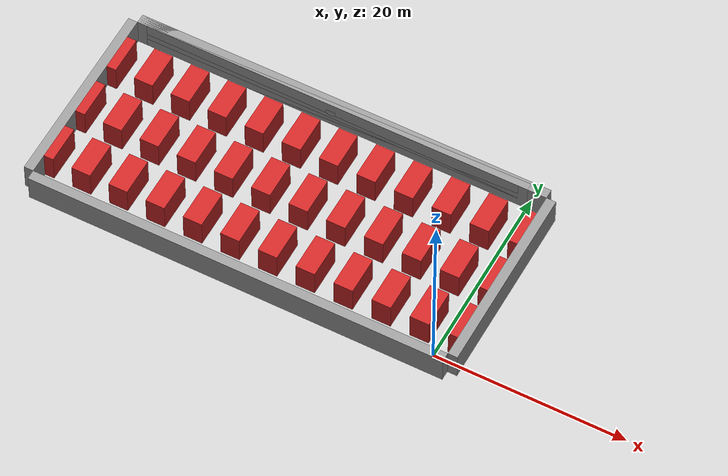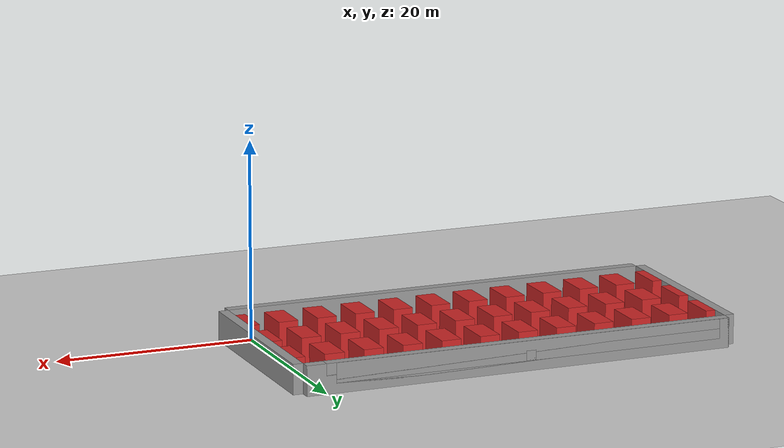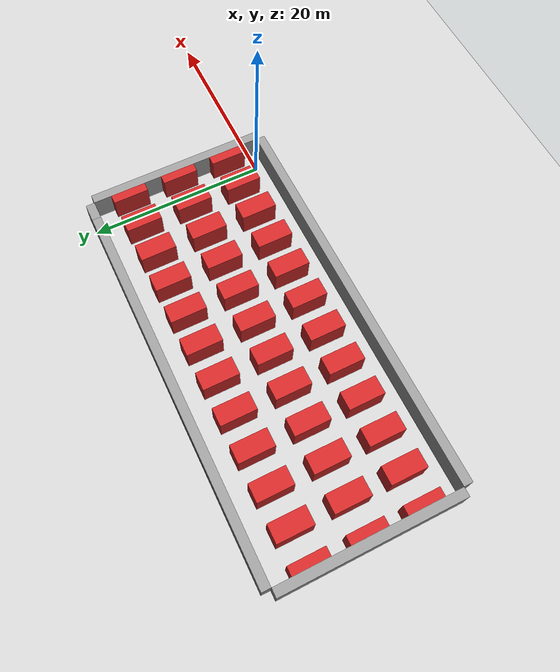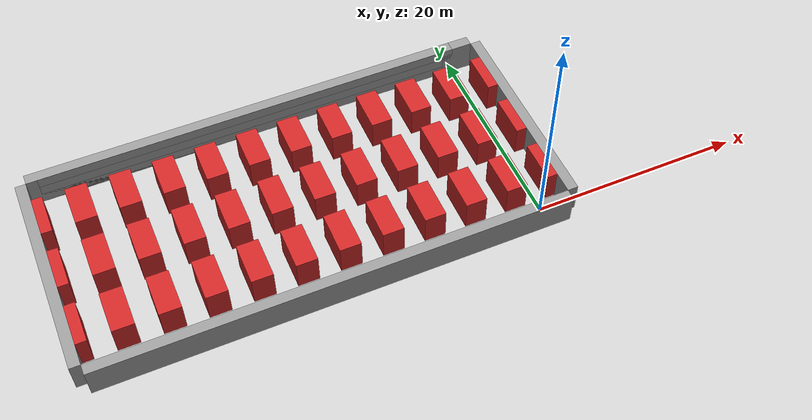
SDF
<sdf version="1.6">
 <world name="default">
  <light name="sun" type="directional">
   <pose>0 0 10 0 -0 0</pose>
   <diffuse>0.8 0.8 0.8 1</diffuse>
   <specular>0.1 0.1 0.1 1</specular>
   <attenuation>
    <range>1000</range>
    <constant>0.9</constant>
    <linear>0.01</linear>
    <quadratic>0.001</quadratic>
   </attenuation>
   <direction>-0.5 0.5 -1</direction>
  </light>
  <model name="ground_plane">
   <static>1</static>
   <link name="link">
    <collision name="collision">
     <geometry><plane><normal>0 0 1</normal><size>100 100</size></plane></geometry>
     <surface><friction><ode><mu>100</mu><mu2>50</mu2></ode></friction></surface>
    </collision>
    <visual name="visual">
     <cast_shadows>0</cast_shadows>
     <geometry><plane><normal>0 0 1</normal><size>100 100</size></plane></geometry>
     <material>
      <script><uri>file://media/materials/scripts/gazebo.material</uri><name>Gazebo/Grey</name></script>
     </material>
    </visual>
   </link>
  </model>
  <gravity>0 0 -9.8</gravity>
  <magnetic_field>6e-06 2.3e-05 -4.2e-05</magnetic_field>
  <atmosphere type="adiabatic"/>
  <physics name="default_physics" default="0" type="ode">
   <max_step_size>0.001</max_step_size>
   <real_time_factor>1</real_time_factor>
   <real_time_update_rate>1000</real_time_update_rate>
  </physics>
  <scene><ambient>0.4 0.4 0.4 1</ambient><background>0.7 0.7 0.7 1</background><shadows>1</shadows></scene>
  <spherical_coordinates>
   <surface_model>EARTH_WGS84</surface_model>
   <latitude_deg>0</latitude_deg>
   <longitude_deg>0</longitude_deg>
   <elevation>0</elevation>
   <heading_deg>0</heading_deg>
  </spherical_coordinates>
  <model name="garage">
   <link name="link">
    <pose>23.5 -0 0 0 -0 0</pose>
    <inertial>
     <mass>1</mass>
     <inertia>
      <ixx>0.166667</ixx>
      <ixy>0</ixy>
      <ixz>0</ixz>
      <iyy>0.166667</iyy>
      <iyz>0</iyz>
      <izz>0.166667</izz>
     </inertia>
    </inertial>
    <kinematic>1</kinematic>
    <gravity>0</gravity>
    <visual name="visual">
     <geometry><box><size>1 20 3</size></box></geometry>
     <material>
      <script><name>Gazebo/Grey</name><uri>file://media/materials/scripts/gazebo.material</uri></script>
      <ambient>0.3 0.3 0.3 1</ambient>
      <diffuse>0.7 0.7 0.7 1</diffuse>
      <specular>0.01 0.01 0.01 1</specular>
      <emissive>0 0 0 1</emissive>
      <shader type="vertex"><normal_map>__default__</normal_map></shader>
     </material>
    </visual>
    <collision name="collision">
     <geometry><box><size>1 20 3</size></box></geometry>
     <surface>
      <friction>
       <ode><mu>1</mu><mu2>1</mu2><fdir1>0 0 0</fdir1><slip1>0</slip1><slip2>0</slip2></ode>
       <torsional>
        <coefficient>1</coefficient>
        <patch_radius>0</patch_radius>
        <surface_radius>0</surface_radius>
        <use_patch_radius>1</use_patch_radius>
        <ode><slip>0</slip></ode>
       </torsional>
      </friction>
      <bounce><restitution_coefficient>0</restitution_coefficient><threshold>1e+06</threshold></bounce>
      <contact>
       <collide_without_contact>0</collide_without_contact>
       <collide_without_contact_bitmask>1</collide_without_contact_bitmask>
       <collide_bitmask>1</collide_bitmask>
       <ode>
        <soft_cfm>0</soft_cfm>
        <soft_erp>0.2</soft_erp>
        <kp>1e+13</kp>
        <kd>1</kd>
        <max_vel>0.01</max_vel>
        <min_depth>0</min_depth>
       </ode>
       <bullet>
        <split_impulse>1</split_impulse>
        <split_impulse_penetration_threshold>-0.01</split_impulse_penetration_threshold>
        <soft_cfm>0</soft_cfm>
        <soft_erp>0.2</soft_erp>
        <kp>1e+13</kp>
        <kd>1</kd>
       </bullet>
      </contact>
     </surface>
    </collision>
   </link>
   <link name="link_0">
    <pose>0 10.5 -0 0 -0 0</pose>
    <inertial>
     <mass>1</mass>
     <inertia>
      <ixx>0.166667</ixx>
      <ixy>0</ixy>
      <ixz>0</ixz>
      <iyy>0.166667</iyy>
      <iyz>0</iyz>
      <izz>0.166667</izz>
     </inertia>
    </inertial>
    <gravity>0</gravity>
    <kinematic>1</kinematic>
    <visual name="ModelPreview_1::link_0::visual_1">
     <geometry><box><size>1 1 1</size></box></geometry>
     <material>
      <lighting>1</lighting>
      <script><uri>file://media/materials/scripts/gazebo.material</uri><name>Gazebo/Grey</name></script>
      <ambient>0.3 0.3 0.3 1</ambient>
      <diffuse>0.7 0.7 0.7 1</diffuse>
      <specular>0.01 0.01 0.01 1</specular>
      <emissive>0 0 0 1</emissive>
      <shader type="vertex"><normal_map>__default__</normal_map></shader>
     </material>
    </visual>
    <visual name="ModelPreview_1::link_0::visual_2">
     <geometry><box><size>40 1 1</size></box></geometry>
     <material>
      <lighting>1</lighting>
      <script><uri>file://media/materials/scripts/gazebo.material</uri><name>Gazebo/Grey</name></script>
      <ambient>0.3 0.3 0.3 1</ambient>
      <diffuse>0.7 0.7 0.7 1</diffuse>
      <specular>0.01 0.01 0.01 1</specular>
      <emissive>0 0 0 1</emissive>
      <shader type="vertex"><normal_map>__default__</normal_map></shader>
     </material>
    </visual>
    <visual name="visual">
     <geometry><box><size>42 1 3</size></box></geometry>
     <material>
      <lighting>1</lighting>
      <script><uri>file://media/materials/scripts/gazebo.material</uri><name>Gazebo/Grey</name></script>
      <ambient>0.3 0.3 0.3 1</ambient>
      <diffuse>0.7 0.7 0.7 1</diffuse>
      <specular>0.01 0.01 0.01 1</specular>
      <emissive>0 0 0 1</emissive>
      <shader type="vertex"><normal_map>__default__</normal_map></shader>
     </material>
    </visual>
    <visual name="ModelPreview_1::link_0::visual_3">
     <geometry><box><size>40 1 2.97</size></box></geometry>
     <material>
      <lighting>1</lighting>
      <script><uri>file://media/materials/scripts/gazebo.material</uri><name>Gazebo/Grey</name></script>
      <ambient>0.3 0.3 0.3 1</ambient>
      <diffuse>0.7 0.7 0.7 1</diffuse>
      <specular>0.01 0.01 0.01 1</specular>
      <emissive>0 0 0 1</emissive>
      <shader type="vertex"><normal_map>__default__</normal_map></shader>
     </material>
    </visual>
    <collision name="collision">
     <geometry><box><size>42 1 3</size></box></geometry>
     <surface>
      <friction>
       <ode><mu>1</mu><mu2>1</mu2><fdir1>0 0 0</fdir1><slip1>0</slip1><slip2>0</slip2></ode>
       <torsional>
        <coefficient>1</coefficient>
        <patch_radius>0</patch_radius>
        <surface_radius>0</surface_radius>
        <use_patch_radius>1</use_patch_radius>
        <ode><slip>0</slip></ode>
       </torsional>
      </friction>
      <bounce><restitution_coefficient>0</restitution_coefficient><threshold>1e+06</threshold></bounce>
      <contact>
       <collide_without_contact>0</collide_without_contact>
       <collide_without_contact_bitmask>1</collide_without_contact_bitmask>
       <collide_bitmask>1</collide_bitmask>
       <ode>
        <soft_cfm>0</soft_cfm>
        <soft_erp>0.2</soft_erp>
        <kp>1e+13</kp>
        <kd>1</kd>
        <max_vel>0.01</max_vel>
        <min_depth>0</min_depth>
       </ode>
       <bullet>
        <split_impulse>1</split_impulse>
        <split_impulse_penetration_threshold>-0.01</split_impulse_penetration_threshold>
        <soft_cfm>0</soft_cfm>
        <soft_erp>0.2</soft_erp>
        <kp>1e+13</kp>
        <kd>1</kd>
       </bullet>
      </contact>
     </surface>
    </collision>
   </link>
   <link name="link_0_clone">
    <pose>1 10.5 -0 0 -0 0</pose>
    <inertial>
     <mass>1</mass>
     <inertia>
      <ixx>0.166667</ixx>
      <ixy>0</ixy>
      <ixz>0</ixz>
      <iyy>0.166667</iyy>
      <iyz>0</iyz>
      <izz>0.166667</izz>
     </inertia>
    </inertial>
    <kinematic>1</kinematic>
    <gravity>0</gravity>
    <visual name="visual">
     <geometry><box><size>44 1 3</size></box></geometry>
     <material>
      <lighting>1</lighting>
      <script><uri>file://media/materials/scripts/gazebo.material</uri><name>Gazebo/Grey</name></script>
      <ambient>0.3 0.3 0.3 1</ambient>
      <diffuse>0.7 0.7 0.7 1</diffuse>
      <specular>0.01 0.01 0.01 1</specular>
      <emissive>0 0 0 1</emissive>
      <shader type="vertex"><normal_map>__default__</normal_map></shader>
     </material>
    </visual>
    <collision name="collision">
     <geometry><box><size>44 1 3</size></box></geometry>
     <surface>
      <friction>
       <ode><mu>1</mu><mu2>1</mu2><fdir1>0 0 0</fdir1><slip1>0</slip1><slip2>0</slip2></ode>
       <torsional>
        <coefficient>1</coefficient>
        <patch_radius>0</patch_radius>
        <surface_radius>0</surface_radius>
        <use_patch_radius>1</use_patch_radius>
        <ode><slip>0</slip></ode>
       </torsional>
      </friction>
      <bounce><restitution_coefficient>0</restitution_coefficient><threshold>1e+06</threshold></bounce>
      <contact>
       <collide_without_contact>0</collide_without_contact>
       <collide_without_contact_bitmask>1</collide_without_contact_bitmask>
       <collide_bitmask>1</collide_bitmask>
       <ode>
        <soft_cfm>0</soft_cfm>
        <soft_erp>0.2</soft_erp>
        <kp>1e+13</kp>
        <kd>1</kd>
        <max_vel>0.01</max_vel>
        <min_depth>0</min_depth>
       </ode>
       <bullet>
        <split_impulse>1</split_impulse>
        <split_impulse_penetration_threshold>-0.01</split_impulse_penetration_threshold>
        <soft_cfm>0</soft_cfm>
        <soft_erp>0.2</soft_erp>
        <kp>1e+13</kp>
        <kd>1</kd>
       </bullet>
      </contact>
     </surface>
    </collision>
   </link>
   <link name="link_0_clone_clone">
    <pose>1 -10.5 -0 0 -0 0</pose>
    <inertial>
     <mass>1</mass>
     <inertia>
      <ixx>0.166667</ixx>
      <ixy>0</ixy>
      <ixz>0</ixz>
      <iyy>0.166667</iyy>
      <iyz>0</iyz>
      <izz>0.166667</izz>
     </inertia>
    </inertial>
    <kinematic>1</kinematic>
    <gravity>0</gravity>
    <visual name="visual">
     <geometry><box><size>44 1 3</size></box></geometry>
     <material>
      <lighting>1</lighting>
      <script><uri>file://media/materials/scripts/gazebo.material</uri><name>Gazebo/Grey</name></script>
      <ambient>0.3 0.3 0.3 1</ambient>
      <diffuse>0.7 0.7 0.7 1</diffuse>
      <specular>0.01 0.01 0.01 1</specular>
      <emissive>0 0 0 1</emissive>
      <shader type="vertex"><normal_map>__default__</normal_map></shader>
     </material>
    </visual>
    <collision name="collision">
     <geometry><box><size>44 1 3</size></box></geometry>
     <surface>
      <friction>
       <ode><mu>1</mu><mu2>1</mu2><fdir1>0 0 0</fdir1><slip1>0</slip1><slip2>0</slip2></ode>
       <torsional>
        <coefficient>1</coefficient>
        <patch_radius>0</patch_radius>
        <surface_radius>0</surface_radius>
        <use_patch_radius>1</use_patch_radius>
        <ode><slip>0</slip></ode>
       </torsional>
      </friction>
      <bounce><restitution_coefficient>0</restitution_coefficient><threshold>1e+06</threshold></bounce>
      <contact>
       <collide_without_contact>0</collide_without_contact>
       <collide_without_contact_bitmask>1</collide_without_contact_bitmask>
       <collide_bitmask>1</collide_bitmask>
       <ode>
        <soft_cfm>0</soft_cfm>
        <soft_erp>0.2</soft_erp>
        <kp>1e+13</kp>
        <kd>1</kd>
        <max_vel>0.01</max_vel>
        <min_depth>0</min_depth>
       </ode>
       <bullet>
        <split_impulse>1</split_impulse>
        <split_impulse_penetration_threshold>-0.01</split_impulse_penetration_threshold>
        <soft_cfm>0</soft_cfm>
        <soft_erp>0.2</soft_erp>
        <kp>1e+13</kp>
        <kd>1</kd>
       </bullet>
      </contact>
     </surface>
    </collision>
   </link>
   <link name="link_1">
    <pose>-20.5 6 -0 0 -0 0</pose>
    <inertial>
     <mass>1</mass>
     <inertia>
      <ixx>0.166667</ixx>
      <ixy>0</ixy>
      <ixz>0</ixz>
      <iyy>0.166667</iyy>
      <iyz>0</iyz>
      <izz>0.166667</izz>
     </inertia>
    </inertial>
    <gravity>0</gravity>
    <kinematic>1</kinematic>
    <visual name="visual">
     <geometry><box><size>1 4 3</size></box></geometry>
     <material>
      <lighting>1</lighting>
      <script><uri>file://media/materials/scripts/gazebo.material</uri><name>Gazebo/Red</name></script>
      <ambient>0.3 0 0 0</ambient>
      <diffuse>0.7 0.7 0.7 1</diffuse>
      <specular>0.01 0.01 0.01 1</specular>
      <emissive>0 0 0 1</emissive>
      <shader type="vertex"><normal_map>__default__</normal_map></shader>
     </material>
    </visual>
    <collision name="collision">
     <geometry><box><size>1 4 3</size></box></geometry>
     <surface>
      <friction>
       <ode><mu>1</mu><mu2>1</mu2><fdir1>0 0 0</fdir1><slip1>0</slip1><slip2>0</slip2></ode>
       <torsional>
        <coefficient>1</coefficient>
        <patch_radius>0</patch_radius>
        <surface_radius>0</surface_radius>
        <use_patch_radius>1</use_patch_radius>
        <ode><slip>0</slip></ode>
       </torsional>
      </friction>
      <bounce><restitution_coefficient>0</restitution_coefficient><threshold>1e+06</threshold></bounce>
      <contact>
       <collide_without_contact>0</collide_without_contact>
       <collide_without_contact_bitmask>1</collide_without_contact_bitmask>
       <collide_bitmask>1</collide_bitmask>
       <ode>
        <soft_cfm>0</soft_cfm>
        <soft_erp>0.2</soft_erp>
        <kp>1e+13</kp>
        <kd>1</kd>
        <max_vel>0.01</max_vel>
        <min_depth>0</min_depth>
       </ode>
       <bullet>
        <split_impulse>1</split_impulse>
        <split_impulse_penetration_threshold>-0.01</split_impulse_penetration_threshold>
        <soft_cfm>0</soft_cfm>
        <soft_erp>0.2</soft_erp>
        <kp>1e+13</kp>
        <kd>1</kd>
       </bullet>
      </contact>
     </surface>
    </collision>
   </link>
   <link name="link_1_clone">
    <pose>-20.5 0 0 0 -0 0</pose>
    <inertial>
     <mass>1</mass>
     <inertia>
      <ixx>0.166667</ixx>
      <ixy>0</ixy>
      <ixz>0</ixz>
      <iyy>0.166667</iyy>
      <iyz>0</iyz>
      <izz>0.166667</izz>
     </inertia>
    </inertial>
    <kinematic>1</kinematic>
    <gravity>0</gravity>
    <visual name="visual">
     <geometry><box><size>1 4 3</size></box></geometry>
     <material>
      <lighting>1</lighting>
      <script><uri>file://media/materials/scripts/gazebo.material</uri><name>Gazebo/Red</name></script>
      <ambient>0.3 0 0 0</ambient>
      <diffuse>0.7 0.7 0.7 1</diffuse>
      <specular>0.01 0.01 0.01 1</specular>
      <emissive>0 0 0 1</emissive>
      <shader type="vertex"><normal_map>__default__</normal_map></shader>
     </material>
    </visual>
    <collision name="collision">
     <geometry><box><size>1 4 3</size></box></geometry>
     <surface>
      <friction>
       <ode><mu>1</mu><mu2>1</mu2><fdir1>0 0 0</fdir1><slip1>0</slip1><slip2>0</slip2></ode>
       <torsional>
        <coefficient>1</coefficient>
        <patch_radius>0</patch_radius>
        <surface_radius>0</surface_radius>
        <use_patch_radius>1</use_patch_radius>
        <ode><slip>0</slip></ode>
       </torsional>
      </friction>
      <bounce><restitution_coefficient>0</restitution_coefficient><threshold>1e+06</threshold></bounce>
      <contact>
       <collide_without_contact>0</collide_without_contact>
       <collide_without_contact_bitmask>1</collide_without_contact_bitmask>
       <collide_bitmask>1</collide_bitmask>
       <ode>
        <soft_cfm>0</soft_cfm>
        <soft_erp>0.2</soft_erp>
        <kp>1e+13</kp>
        <kd>1</kd>
        <max_vel>0.01</max_vel>
        <min_depth>0</min_depth>
       </ode>
       <bullet>
        <split_impulse>1</split_impulse>
        <split_impulse_penetration_threshold>-0.01</split_impulse_penetration_threshold>
        <soft_cfm>0</soft_cfm>
        <soft_erp>0.2</soft_erp>
        <kp>1e+13</kp>
        <kd>1</kd>
       </bullet>
      </contact>
     </surface>
    </collision>
   </link>
   <link name="link_1_clone_0">
    <pose>-20.5 -6 0 0 -0 0</pose>
    <inertial>
     <mass>1</mass>
     <inertia>
      <ixx>0.166667</ixx>
      <ixy>0</ixy>
      <ixz>0</ixz>
      <iyy>0.166667</iyy>
      <iyz>0</iyz>
      <izz>0.166667</izz>
     </inertia>
    </inertial>
    <kinematic>1</kinematic>
    <gravity>0</gravity>
    <visual name="visual">
     <geometry><box><size>1 4 3</size></box></geometry>
     <material>
      <lighting>1</lighting>
      <script><uri>file://media/materials/scripts/gazebo.material</uri><name>Gazebo/Red</name></script>
      <ambient>0.3 0 0 0</ambient>
      <diffuse>0.7 0.7 0.7 1</diffuse>
      <specular>0.01 0.01 0.01 1</specular>
      <emissive>0 0 0 1</emissive>
      <shader type="vertex"><normal_map>__default__</normal_map></shader>
     </material>
    </visual>
    <collision name="collision">
     <geometry><box><size>1 4 3</size></box></geometry>
     <surface>
      <friction>
       <ode><mu>1</mu><mu2>1</mu2><fdir1>0 0 0</fdir1><slip1>0</slip1><slip2>0</slip2></ode>
       <torsional>
        <coefficient>1</coefficient>
        <patch_radius>0</patch_radius>
        <surface_radius>0</surface_radius>
        <use_patch_radius>1</use_patch_radius>
        <ode><slip>0</slip></ode>
       </torsional>
      </friction>
      <bounce><restitution_coefficient>0</restitution_coefficient><threshold>1e+06</threshold></bounce>
      <contact>
       <collide_without_contact>0</collide_without_contact>
       <collide_without_contact_bitmask>1</collide_without_contact_bitmask>
       <collide_bitmask>1</collide_bitmask>
       <ode>
        <soft_cfm>0</soft_cfm>
        <soft_erp>0.2</soft_erp>
        <kp>1e+13</kp>
        <kd>1</kd>
        <max_vel>0.01</max_vel>
        <min_depth>0</min_depth>
       </ode>
       <bullet>
        <split_impulse>1</split_impulse>
        <split_impulse_penetration_threshold>-0.01</split_impulse_penetration_threshold>
        <soft_cfm>0</soft_cfm>
        <soft_erp>0.2</soft_erp>
        <kp>1e+13</kp>
        <kd>1</kd>
       </bullet>
      </contact>
     </surface>
    </collision>
   </link>
   <link name="link_1_clone_1">
    <pose>-17 6 -0 0 -0 0</pose>
    <inertial>
     <mass>1</mass>
     <inertia>
      <ixx>0.166667</ixx>
      <ixy>0</ixy>
      <ixz>0</ixz>
      <iyy>0.166667</iyy>
      <iyz>0</iyz>
      <izz>0.166667</izz>
     </inertia>
    </inertial>
    <kinematic>1</kinematic>
    <gravity>0</gravity>
    <visual name="visual">
     <geometry><box><size>2 4 3</size></box></geometry>
     <material>
      <lighting>1</lighting>
      <script><uri>file://media/materials/scripts/gazebo.material</uri><name>Gazebo/Red</name></script>
      <ambient>0 0.3 0 1</ambient>
      <diffuse>0.7 0.7 0.7 1</diffuse>
      <specular>0.01 0.01 0.01 1</specular>
      <emissive>0 0 0 1</emissive>
      <shader type="vertex"><normal_map>__default__</normal_map></shader>
     </material>
    </visual>
    <collision name="collision">
     <geometry><box><size>2 4 3</size></box></geometry>
     <surface>
      <friction>
       <ode><mu>1</mu><mu2>1</mu2><fdir1>0 0 0</fdir1><slip1>0</slip1><slip2>0</slip2></ode>
       <torsional>
        <coefficient>1</coefficient>
        <patch_radius>0</patch_radius>
        <surface_radius>0</surface_radius>
        <use_patch_radius>1</use_patch_radius>
        <ode><slip>0</slip></ode>
       </torsional>
      </friction>
      <bounce><restitution_coefficient>0</restitution_coefficient><threshold>1e+06</threshold></bounce>
      <contact>
       <collide_without_contact>0</collide_without_contact>
       <collide_without_contact_bitmask>1</collide_without_contact_bitmask>
       <collide_bitmask>1</collide_bitmask>
       <ode>
        <soft_cfm>0</soft_cfm>
        <soft_erp>0.2</soft_erp>
        <kp>1e+13</kp>
        <kd>1</kd>
        <max_vel>0.01</max_vel>
        <min_depth>0</min_depth>
       </ode>
       <bullet>
        <split_impulse>1</split_impulse>
        <split_impulse_penetration_threshold>-0.01</split_impulse_penetration_threshold>
        <soft_cfm>0</soft_cfm>
        <soft_erp>0.2</soft_erp>
        <kp>1e+13</kp>
        <kd>1</kd>
       </bullet>
      </contact>
     </surface>
    </collision>
   </link>
   <link name="link_1_clone_1_clone">
    <pose>-17 0 -0 0 -0 0</pose>
    <inertial>
     <mass>1</mass>
     <inertia>
      <ixx>0.166667</ixx>
      <ixy>0</ixy>
      <ixz>0</ixz>
      <iyy>0.166667</iyy>
      <iyz>0</iyz>
      <izz>0.166667</izz>
     </inertia>
    </inertial>
    <kinematic>1</kinematic>
    <gravity>0</gravity>
    <visual name="visual">
     <geometry><box><size>2 4 3</size></box></geometry>
     <material>
      <lighting>1</lighting>
      <script><uri>file://media/materials/scripts/gazebo.material</uri><name>Gazebo/Red</name></script>
      <ambient>0 0.3 0 1</ambient>
      <diffuse>0.7 0.7 0.7 1</diffuse>
      <specular>0.01 0.01 0.01 1</specular>
      <emissive>0 0 0 1</emissive>
      <shader type="vertex"><normal_map>__default__</normal_map></shader>
     </material>
    </visual>
    <collision name="collision">
     <geometry><box><size>2 4 3</size></box></geometry>
     <surface>
      <friction>
       <ode><mu>1</mu><mu2>1</mu2><fdir1>0 0 0</fdir1><slip1>0</slip1><slip2>0</slip2></ode>
       <torsional>
        <coefficient>1</coefficient>
        <patch_radius>0</patch_radius>
        <surface_radius>0</surface_radius>
        <use_patch_radius>1</use_patch_radius>
        <ode><slip>0</slip></ode>
       </torsional>
      </friction>
      <bounce><restitution_coefficient>0</restitution_coefficient><threshold>1e+06</threshold></bounce>
      <contact>
       <collide_without_contact>0</collide_without_contact>
       <collide_without_contact_bitmask>1</collide_without_contact_bitmask>
       <collide_bitmask>1</collide_bitmask>
       <ode>
        <soft_cfm>0</soft_cfm>
        <soft_erp>0.2</soft_erp>
        <kp>1e+13</kp>
        <kd>1</kd>
        <max_vel>0.01</max_vel>
        <min_depth>0</min_depth>
       </ode>
       <bullet>
        <split_impulse>1</split_impulse>
        <split_impulse_penetration_threshold>-0.01</split_impulse_penetration_threshold>
        <soft_cfm>0</soft_cfm>
        <soft_erp>0.2</soft_erp>
        <kp>1e+13</kp>
        <kd>1</kd>
       </bullet>
      </contact>
     </surface>
    </collision>
   </link>
   <link name="link_1_clone_1_clone_0">
    <pose>-17 -6 -0 0 -0 0</pose>
    <inertial>
     <mass>1</mass>
     <inertia>
      <ixx>0.166667</ixx>
      <ixy>0</ixy>
      <ixz>0</ixz>
      <iyy>0.166667</iyy>
      <iyz>0</iyz>
      <izz>0.166667</izz>
     </inertia>
    </inertial>
    <kinematic>1</kinematic>
    <visual name="visual">
     <geometry><box><size>2 4 3</size></box></geometry>
     <material>
      <lighting>1</lighting>
      <script><uri>file://media/materials/scripts/gazebo.material</uri><name>Gazebo/Red</name></script>
      <ambient>0 0.3 0 1</ambient>
      <diffuse>0.7 0.7 0.7 1</diffuse>
      <specular>0.01 0.01 0.01 1</specular>
      <emissive>0 0 0 1</emissive>
      <shader type="vertex"><normal_map>__default__</normal_map></shader>
     </material>
    </visual>
    <collision name="collision">
     <geometry><box><size>2 4 3</size></box></geometry>
     <surface>
      <friction>
       <ode><mu>1</mu><mu2>1</mu2><fdir1>0 0 0</fdir1><slip1>0</slip1><slip2>0</slip2></ode>
       <torsional>
        <coefficient>1</coefficient>
        <patch_radius>0</patch_radius>
        <surface_radius>0</surface_radius>
        <use_patch_radius>1</use_patch_radius>
        <ode><slip>0</slip></ode>
       </torsional>
      </friction>
      <bounce><restitution_coefficient>0</restitution_coefficient><threshold>1e+06</threshold></bounce>
      <contact>
       <collide_without_contact>0</collide_without_contact>
       <collide_without_contact_bitmask>1</collide_without_contact_bitmask>
       <collide_bitmask>1</collide_bitmask>
       <ode>
        <soft_cfm>0</soft_cfm>
        <soft_erp>0.2</soft_erp>
        <kp>1e+13</kp>
        <kd>1</kd>
        <max_vel>0.01</max_vel>
        <min_depth>0</min_depth>
       </ode>
       <bullet>
        <split_impulse>1</split_impulse>
        <split_impulse_penetration_threshold>-0.01</split_impulse_penetration_threshold>
        <soft_cfm>0</soft_cfm>
        <soft_erp>0.2</soft_erp>
        <kp>1e+13</kp>
        <kd>1</kd>
       </bullet>
      </contact>
     </surface>
    </collision>
   </link>
   <link name="link_1_clone_1_clone_1">
    <pose>-13 -6 -0 0 -0 0</pose>
    <inertial>
     <mass>1</mass>
     <inertia>
      <ixx>0.166667</ixx>
      <ixy>0</ixy>
      <ixz>0</ixz>
      <iyy>0.166667</iyy>
      <iyz>0</iyz>
      <izz>0.166667</izz>
     </inertia>
    </inertial>
    <kinematic>1</kinematic>
    <gravity>0</gravity>
    <visual name="visual">
     <geometry><box><size>2 4 3</size></box></geometry>
     <material>
      <lighting>1</lighting>
      <script><uri>file://media/materials/scripts/gazebo.material</uri><name>Gazebo/Red</name></script>
      <ambient>0 0 0.3 1</ambient>
      <diffuse>0.7 0.7 0.7 1</diffuse>
      <specular>0.01 0.01 0.01 1</specular>
      <emissive>0 0 0 1</emissive>
      <shader type="vertex"><normal_map>__default__</normal_map></shader>
     </material>
    </visual>
    <collision name="collision">
     <geometry><box><size>2 4 3</size></box></geometry>
     <surface>
      <friction>
       <ode><mu>1</mu><mu2>1</mu2><fdir1>0 0 0</fdir1><slip1>0</slip1><slip2>0</slip2></ode>
       <torsional>
        <coefficient>1</coefficient>
        <patch_radius>0</patch_radius>
        <surface_radius>0</surface_radius>
        <use_patch_radius>1</use_patch_radius>
        <ode><slip>0</slip></ode>
       </torsional>
      </friction>
      <bounce><restitution_coefficient>0</restitution_coefficient><threshold>1e+06</threshold></bounce>
      <contact>
       <collide_without_contact>0</collide_without_contact>
       <collide_without_contact_bitmask>1</collide_without_contact_bitmask>
       <collide_bitmask>1</collide_bitmask>
       <ode>
        <soft_cfm>0</soft_cfm>
        <soft_erp>0.2</soft_erp>
        <kp>1e+13</kp>
        <kd>1</kd>
        <max_vel>0.01</max_vel>
        <min_depth>0</min_depth>
       </ode>
       <bullet>
        <split_impulse>1</split_impulse>
        <split_impulse_penetration_threshold>-0.01</split_impulse_penetration_threshold>
        <soft_cfm>0</soft_cfm>
        <soft_erp>0.2</soft_erp>
        <kp>1e+13</kp>
        <kd>1</kd>
       </bullet>
      </contact>
     </surface>
    </collision>
   </link>
   <link name="link_1_clone_1_clone_1_clone">
    <pose>-13 0 0 0 -0 0</pose>
    <inertial>
     <mass>1</mass>
     <inertia>
      <ixx>0.166667</ixx>
      <ixy>0</ixy>
      <ixz>0</ixz>
      <iyy>0.166667</iyy>
      <iyz>0</iyz>
      <izz>0.166667</izz>
     </inertia>
    </inertial>
    <kinematic>1</kinematic>
    <gravity>0</gravity>
    <visual name="visual">
     <geometry><box><size>2 4 3</size></box></geometry>
     <material>
      <lighting>1</lighting>
      <script><uri>file://media/materials/scripts/gazebo.material</uri><name>Gazebo/Red</name></script>
      <ambient>0 0 0.3 1</ambient>
      <diffuse>0.7 0.7 0.7 1</diffuse>
      <specular>0.01 0.01 0.01 1</specular>
      <emissive>0 0 0 1</emissive>
      <shader type="vertex"><normal_map>__default__</normal_map></shader>
     </material>
    </visual>
    <collision name="collision">
     <geometry><box><size>2 4 3</size></box></geometry>
     <surface>
      <friction>
       <ode><mu>1</mu><mu2>1</mu2><fdir1>0 0 0</fdir1><slip1>0</slip1><slip2>0</slip2></ode>
       <torsional>
        <coefficient>1</coefficient>
        <patch_radius>0</patch_radius>
        <surface_radius>0</surface_radius>
        <use_patch_radius>1</use_patch_radius>
        <ode><slip>0</slip></ode>
       </torsional>
      </friction>
      <bounce><restitution_coefficient>0</restitution_coefficient><threshold>1e+06</threshold></bounce>
      <contact>
       <collide_without_contact>0</collide_without_contact>
       <collide_without_contact_bitmask>1</collide_without_contact_bitmask>
       <collide_bitmask>1</collide_bitmask>
       <ode>
        <soft_cfm>0</soft_cfm>
        <soft_erp>0.2</soft_erp>
        <kp>1e+13</kp>
        <kd>1</kd>
        <max_vel>0.01</max_vel>
        <min_depth>0</min_depth>
       </ode>
       <bullet>
        <split_impulse>1</split_impulse>
        <split_impulse_penetration_threshold>-0.01</split_impulse_penetration_threshold>
        <soft_cfm>0</soft_cfm>
        <soft_erp>0.2</soft_erp>
        <kp>1e+13</kp>
        <kd>1</kd>
       </bullet>
      </contact>
     </surface>
    </collision>
   </link>
   <link name="link_1_clone_1_clone_1_clone_0">
    <pose>-13 6 0 0 -0 0</pose>
    <inertial>
     <mass>1</mass>
     <inertia>
      <ixx>0.166667</ixx>
      <ixy>0</ixy>
      <ixz>0</ixz>
      <iyy>0.166667</iyy>
      <iyz>0</iyz>
      <izz>0.166667</izz>
     </inertia>
    </inertial>
    <kinematic>1</kinematic>
    <gravity>0</gravity>
    <visual name="visual">
     <geometry><box><size>2 4 3</size></box></geometry>
     <material>
      <lighting>1</lighting>
      <script><uri>file://media/materials/scripts/gazebo.material</uri><name>Gazebo/Red</name></script>
      <ambient>0 0 0.3 1</ambient>
      <diffuse>0.7 0.7 0.7 1</diffuse>
      <specular>0.01 0.01 0.01 1</specular>
      <emissive>0 0 0 1</emissive>
      <shader type="vertex"><normal_map>__default__</normal_map></shader>
     </material>
    </visual>
    <collision name="collision">
     <geometry><box><size>2 4 3</size></box></geometry>
     <surface>
      <friction>
       <ode><mu>1</mu><mu2>1</mu2><fdir1>0 0 0</fdir1><slip1>0</slip1><slip2>0</slip2></ode>
       <torsional>
        <coefficient>1</coefficient>
        <patch_radius>0</patch_radius>
        <surface_radius>0</surface_radius>
        <use_patch_radius>1</use_patch_radius>
        <ode><slip>0</slip></ode>
       </torsional>
      </friction>
      <bounce><restitution_coefficient>0</restitution_coefficient><threshold>1e+06</threshold></bounce>
      <contact>
       <collide_without_contact>0</collide_without_contact>
       <collide_without_contact_bitmask>1</collide_without_contact_bitmask>
       <collide_bitmask>1</collide_bitmask>
       <ode>
        <soft_cfm>0</soft_cfm>
        <soft_erp>0.2</soft_erp>
        <kp>1e+13</kp>
        <kd>1</kd>
        <max_vel>0.01</max_vel>
        <min_depth>0</min_depth>
       </ode>
       <bullet>
        <split_impulse>1</split_impulse>
        <split_impulse_penetration_threshold>-0.01</split_impulse_penetration_threshold>
        <soft_cfm>0</soft_cfm>
        <soft_erp>0.2</soft_erp>
        <kp>1e+13</kp>
        <kd>1</kd>
       </bullet>
      </contact>
     </surface>
    </collision>
   </link>
   <link name="link_1_clone_1_clone_1_clone_0_clone">
    <pose>-9 6 -0 0 -0 0</pose>
    <inertial>
     <mass>1</mass>
     <inertia>
      <ixx>0.166667</ixx>
      <ixy>0</ixy>
      <ixz>0</ixz>
      <iyy>0.166667</iyy>
      <iyz>0</iyz>
      <izz>0.166667</izz>
     </inertia>
    </inertial>
    <kinematic>1</kinematic>
    <visual name="visual">
     <geometry><box><size>2 4 3</size></box></geometry>
     <material>
      <lighting>1</lighting>
      <script><uri>file://media/materials/scripts/gazebo.material</uri><name>Gazebo/Red</name></script>
      <ambient>0 0 0.1 0.9</ambient>
      <diffuse>0.7 0.7 0.7 1</diffuse>
      <specular>0.01 0.01 0.01 1</specular>
      <emissive>0 0 0 1</emissive>
      <shader type="vertex"><normal_map>__default__</normal_map></shader>
     </material>
    </visual>
    <collision name="collision">
     <geometry><box><size>2 4 3</size></box></geometry>
     <surface>
      <friction>
       <ode><mu>1</mu><mu2>1</mu2><fdir1>0 0 0</fdir1><slip1>0</slip1><slip2>0</slip2></ode>
       <torsional>
        <coefficient>1</coefficient>
        <patch_radius>0</patch_radius>
        <surface_radius>0</surface_radius>
        <use_patch_radius>1</use_patch_radius>
        <ode><slip>0</slip></ode>
       </torsional>
      </friction>
      <bounce><restitution_coefficient>0</restitution_coefficient><threshold>1e+06</threshold></bounce>
      <contact>
       <collide_without_contact>0</collide_without_contact>
       <collide_without_contact_bitmask>1</collide_without_contact_bitmask>
       <collide_bitmask>1</collide_bitmask>
       <ode>
        <soft_cfm>0</soft_cfm>
        <soft_erp>0.2</soft_erp>
        <kp>1e+13</kp>
        <kd>1</kd>
        <max_vel>0.01</max_vel>
        <min_depth>0</min_depth>
       </ode>
       <bullet>
        <split_impulse>1</split_impulse>
        <split_impulse_penetration_threshold>-0.01</split_impulse_penetration_threshold>
        <soft_cfm>0</soft_cfm>
        <soft_erp>0.2</soft_erp>
        <kp>1e+13</kp>
        <kd>1</kd>
       </bullet>
      </contact>
     </surface>
    </collision>
   </link>
   <link name="link_1_clone_1_clone_1_clone_0_clone_clone">
    <pose>-9 0 0 0 -0 0</pose>
    <inertial>
     <mass>1</mass>
     <inertia>
      <ixx>0.166667</ixx>
      <ixy>0</ixy>
      <ixz>0</ixz>
      <iyy>0.166667</iyy>
      <iyz>0</iyz>
      <izz>0.166667</izz>
     </inertia>
    </inertial>
    <kinematic>1</kinematic>
    <gravity>0</gravity>
    <visual name="visual">
     <geometry><box><size>2 4 3</size></box></geometry>
     <material>
      <lighting>1</lighting>
      <script><uri>file://media/materials/scripts/gazebo.material</uri><name>Gazebo/Red</name></script>
      <ambient>0 0 0.1 0.9</ambient>
      <diffuse>0.7 0.7 0.7 1</diffuse>
      <specular>0.01 0.01 0.01 1</specular>
      <emissive>0 0 0 1</emissive>
      <shader type="vertex"><normal_map>__default__</normal_map></shader>
     </material>
    </visual>
    <collision name="collision">
     <geometry><box><size>2 4 3</size></box></geometry>
     <surface>
      <friction>
       <ode><mu>1</mu><mu2>1</mu2><fdir1>0 0 0</fdir1><slip1>0</slip1><slip2>0</slip2></ode>
       <torsional>
        <coefficient>1</coefficient>
        <patch_radius>0</patch_radius>
        <surface_radius>0</surface_radius>
        <use_patch_radius>1</use_patch_radius>
        <ode><slip>0</slip></ode>
       </torsional>
      </friction>
      <bounce><restitution_coefficient>0</restitution_coefficient><threshold>1e+06</threshold></bounce>
      <contact>
       <collide_without_contact>0</collide_without_contact>
       <collide_without_contact_bitmask>1</collide_without_contact_bitmask>
       <collide_bitmask>1</collide_bitmask>
       <ode>
        <soft_cfm>0</soft_cfm>
        <soft_erp>0.2</soft_erp>
        <kp>1e+13</kp>
        <kd>1</kd>
        <max_vel>0.01</max_vel>
        <min_depth>0</min_depth>
       </ode>
       <bullet>
        <split_impulse>1</split_impulse>
        <split_impulse_penetration_threshold>-0.01</split_impulse_penetration_threshold>
        <soft_cfm>0</soft_cfm>
        <soft_erp>0.2</soft_erp>
        <kp>1e+13</kp>
        <kd>1</kd>
       </bullet>
      </contact>
     </surface>
    </collision>
   </link>
   <link name="link_1_clone_1_clone_1_clone_0_clone_clone_0">
    <pose>-9 -6 -0 0 -0 0</pose>
    <inertial>
     <mass>1</mass>
     <inertia>
      <ixx>0.166667</ixx>
      <ixy>0</ixy>
      <ixz>0</ixz>
      <iyy>0.166667</iyy>
      <iyz>0</iyz>
      <izz>0.166667</izz>
     </inertia>
    </inertial>
    <kinematic>1</kinematic>
    <visual name="visual">
     <geometry><box><size>2 4 3</size></box></geometry>
     <material>
      <lighting>1</lighting>
      <script><uri>file://media/materials/scripts/gazebo.material</uri><name>Gazebo/Red</name></script>
      <ambient>0 0 0.1 0.9</ambient>
      <diffuse>0.7 0.7 0.7 1</diffuse>
      <specular>0.01 0.01 0.01 1</specular>
      <emissive>0 0 0 1</emissive>
      <shader type="vertex"><normal_map>__default__</normal_map></shader>
     </material>
    </visual>
    <collision name="collision">
     <geometry><box><size>2 4 3</size></box></geometry>
     <surface>
      <friction>
       <ode><mu>1</mu><mu2>1</mu2><fdir1>0 0 0</fdir1><slip1>0</slip1><slip2>0</slip2></ode>
       <torsional>
        <coefficient>1</coefficient>
        <patch_radius>0</patch_radius>
        <surface_radius>0</surface_radius>
        <use_patch_radius>1</use_patch_radius>
        <ode><slip>0</slip></ode>
       </torsional>
      </friction>
      <bounce><restitution_coefficient>0</restitution_coefficient><threshold>1e+06</threshold></bounce>
      <contact>
       <collide_without_contact>0</collide_without_contact>
       <collide_without_contact_bitmask>1</collide_without_contact_bitmask>
       <collide_bitmask>1</collide_bitmask>
       <ode>
        <soft_cfm>0</soft_cfm>
        <soft_erp>0.2</soft_erp>
        <kp>1e+13</kp>
        <kd>1</kd>
        <max_vel>0.01</max_vel>
        <min_depth>0</min_depth>
       </ode>
       <bullet>
        <split_impulse>1</split_impulse>
        <split_impulse_penetration_threshold>-0.01</split_impulse_penetration_threshold>
        <soft_cfm>0</soft_cfm>
        <soft_erp>0.2</soft_erp>
        <kp>1e+13</kp>
        <kd>1</kd>
       </bullet>
      </contact>
     </surface>
    </collision>
   </link>
   <link name="link_1_clone_1_clone_1_clone_0_clone_clone_1">
    <pose>-5 -6 0 0 -0 0</pose>
    <inertial>
     <mass>1</mass>
     <inertia>
      <ixx>0.166667</ixx>
      <ixy>0</ixy>
      <ixz>0</ixz>
      <iyy>0.166667</iyy>
      <iyz>0</iyz>
      <izz>0.166667</izz>
     </inertia>
    </inertial>
    <kinematic>1</kinematic>
    <gravity>0</gravity>
    <visual name="visual">
     <geometry><box><size>2 4 3</size></box></geometry>
     <material>
      <lighting>1</lighting>
      <script><uri>file://media/materials/scripts/gazebo.material</uri><name>Gazebo/Red</name></script>
      <ambient>0.9 0 0.1 0.5</ambient>
      <diffuse>0.7 0.7 0.7 1</diffuse>
      <specular>0.01 0.01 0.01 1</specular>
      <emissive>0 0 0 1</emissive>
      <shader type="vertex"><normal_map>__default__</normal_map></shader>
     </material>
    </visual>
    <collision name="collision">
     <geometry><box><size>2 4 3</size></box></geometry>
     <surface>
      <friction>
       <ode><mu>1</mu><mu2>1</mu2><fdir1>0 0 0</fdir1><slip1>0</slip1><slip2>0</slip2></ode>
       <torsional>
        <coefficient>1</coefficient>
        <patch_radius>0</patch_radius>
        <surface_radius>0</surface_radius>
        <use_patch_radius>1</use_patch_radius>
        <ode><slip>0</slip></ode>
       </torsional>
      </friction>
      <bounce><restitution_coefficient>0</restitution_coefficient><threshold>1e+06</threshold></bounce>
      <contact>
       <collide_without_contact>0</collide_without_contact>
       <collide_without_contact_bitmask>1</collide_without_contact_bitmask>
       <collide_bitmask>1</collide_bitmask>
       <ode>
        <soft_cfm>0</soft_cfm>
        <soft_erp>0.2</soft_erp>
        <kp>1e+13</kp>
        <kd>1</kd>
        <max_vel>0.01</max_vel>
        <min_depth>0</min_depth>
       </ode>
       <bullet>
        <split_impulse>1</split_impulse>
        <split_impulse_penetration_threshold>-0.01</split_impulse_penetration_threshold>
        <soft_cfm>0</soft_cfm>
        <soft_erp>0.2</soft_erp>
        <kp>1e+13</kp>
        <kd>1</kd>
       </bullet>
      </contact>
     </surface>
    </collision>
   </link>
   <link name="link_1_clone_1_clone_1_clone_0_clone_clone_1_clone">
    <pose>-5 0 -0 0 -0 0</pose>
    <inertial>
     <mass>1</mass>
     <inertia>
      <ixx>0.166667</ixx>
      <ixy>0</ixy>
      <ixz>0</ixz>
      <iyy>0.166667</iyy>
      <iyz>0</iyz>
      <izz>0.166667</izz>
     </inertia>
    </inertial>
    <kinematic>1</kinematic>
    <visual name="visual">
     <geometry><box><size>2 4 3</size></box></geometry>
     <material>
      <lighting>1</lighting>
      <script><uri>file://media/materials/scripts/gazebo.material</uri><name>Gazebo/Red</name></script>
      <ambient>0.9 0 0.1 0.5</ambient>
      <diffuse>0.7 0.7 0.7 1</diffuse>
      <specular>0.01 0.01 0.01 1</specular>
      <emissive>0 0 0 1</emissive>
      <shader type="vertex"><normal_map>__default__</normal_map></shader>
     </material>
    </visual>
    <collision name="collision">
     <geometry><box><size>2 4 3</size></box></geometry>
     <surface>
      <friction>
       <ode><mu>1</mu><mu2>1</mu2><fdir1>0 0 0</fdir1><slip1>0</slip1><slip2>0</slip2></ode>
       <torsional>
        <coefficient>1</coefficient>
        <patch_radius>0</patch_radius>
        <surface_radius>0</surface_radius>
        <use_patch_radius>1</use_patch_radius>
        <ode><slip>0</slip></ode>
       </torsional>
      </friction>
      <bounce><restitution_coefficient>0</restitution_coefficient><threshold>1e+06</threshold></bounce>
      <contact>
       <collide_without_contact>0</collide_without_contact>
       <collide_without_contact_bitmask>1</collide_without_contact_bitmask>
       <collide_bitmask>1</collide_bitmask>
       <ode>
        <soft_cfm>0</soft_cfm>
        <soft_erp>0.2</soft_erp>
        <kp>1e+13</kp>
        <kd>1</kd>
        <max_vel>0.01</max_vel>
        <min_depth>0</min_depth>
       </ode>
       <bullet>
        <split_impulse>1</split_impulse>
        <split_impulse_penetration_threshold>-0.01</split_impulse_penetration_threshold>
        <soft_cfm>0</soft_cfm>
        <soft_erp>0.2</soft_erp>
        <kp>1e+13</kp>
        <kd>1</kd>
       </bullet>
      </contact>
     </surface>
    </collision>
   </link>
   <link name="link_1_clone_1_clone_1_clone_0_clone_clone_1_clone_0">
    <pose>-5 6 0 0 -0 0</pose>
    <inertial>
     <mass>1</mass>
     <inertia>
      <ixx>0.166667</ixx>
      <ixy>0</ixy>
      <ixz>0</ixz>
      <iyy>0.166667</iyy>
      <iyz>0</iyz>
      <izz>0.166667</izz>
     </inertia>
    </inertial>
    <kinematic>1</kinematic>
    <visual name="visual">
     <geometry><box><size>2 4 3</size></box></geometry>
     <material>
      <lighting>1</lighting>
      <script><uri>file://media/materials/scripts/gazebo.material</uri><name>Gazebo/Red</name></script>
      <ambient>0.9 0 0.1 0.5</ambient>
      <diffuse>0.7 0.7 0.7 1</diffuse>
      <specular>0.01 0.01 0.01 1</specular>
      <emissive>0 0 0 1</emissive>
      <shader type="vertex"><normal_map>__default__</normal_map></shader>
     </material>
    </visual>
    <collision name="collision">
     <geometry><box><size>2 4 3</size></box></geometry>
     <surface>
      <friction>
       <ode><mu>1</mu><mu2>1</mu2><fdir1>0 0 0</fdir1><slip1>0</slip1><slip2>0</slip2></ode>
       <torsional>
        <coefficient>1</coefficient>
        <patch_radius>0</patch_radius>
        <surface_radius>0</surface_radius>
        <use_patch_radius>1</use_patch_radius>
        <ode><slip>0</slip></ode>
       </torsional>
      </friction>
      <bounce><restitution_coefficient>0</restitution_coefficient><threshold>1e+06</threshold></bounce>
      <contact>
       <collide_without_contact>0</collide_without_contact>
       <collide_without_contact_bitmask>1</collide_without_contact_bitmask>
       <collide_bitmask>1</collide_bitmask>
       <ode>
        <soft_cfm>0</soft_cfm>
        <soft_erp>0.2</soft_erp>
        <kp>1e+13</kp>
        <kd>1</kd>
        <max_vel>0.01</max_vel>
        <min_depth>0</min_depth>
       </ode>
       <bullet>
        <split_impulse>1</split_impulse>
        <split_impulse_penetration_threshold>-0.01</split_impulse_penetration_threshold>
        <soft_cfm>0</soft_cfm>
        <soft_erp>0.2</soft_erp>
        <kp>1e+13</kp>
        <kd>1</kd>
       </bullet>
      </contact>
     </surface>
    </collision>
   </link>
   <link name="link_1_clone_1_clone_1_clone_0_clone_clone_1_clone_1">
    <pose>-1 6 0 0 -0 0</pose>
    <inertial>
     <mass>1</mass>
     <inertia>
      <ixx>0.166667</ixx>
      <ixy>0</ixy>
      <ixz>0</ixz>
      <iyy>0.166667</iyy>
      <iyz>0</iyz>
      <izz>0.166667</izz>
     </inertia>
    </inertial>
    <kinematic>1</kinematic>
    <gravity>0</gravity>
    <visual name="visual">
     <geometry><box><size>2 4 3</size></box></geometry>
     <material>
      <lighting>1</lighting>
      <script><uri>file://media/materials/scripts/gazebo.material</uri><name>Gazebo/Red</name></script>
      <ambient>0.2 0.8 0.8 0.5</ambient>
      <diffuse>0.7 0.7 0.7 1</diffuse>
      <specular>0.01 0.01 0.01 1</specular>
      <emissive>0 0 0 1</emissive>
      <shader type="vertex"><normal_map>__default__</normal_map></shader>
     </material>
    </visual>
    <collision name="collision">
     <geometry><box><size>2 4 3</size></box></geometry>
     <surface>
      <friction>
       <ode><mu>1</mu><mu2>1</mu2><fdir1>0 0 0</fdir1><slip1>0</slip1><slip2>0</slip2></ode>
       <torsional>
        <coefficient>1</coefficient>
        <patch_radius>0</patch_radius>
        <surface_radius>0</surface_radius>
        <use_patch_radius>1</use_patch_radius>
        <ode><slip>0</slip></ode>
       </torsional>
      </friction>
      <bounce><restitution_coefficient>0</restitution_coefficient><threshold>1e+06</threshold></bounce>
      <contact>
       <collide_without_contact>0</collide_without_contact>
       <collide_without_contact_bitmask>1</collide_without_contact_bitmask>
       <collide_bitmask>1</collide_bitmask>
       <ode>
        <soft_cfm>0</soft_cfm>
        <soft_erp>0.2</soft_erp>
        <kp>1e+13</kp>
        <kd>1</kd>
        <max_vel>0.01</max_vel>
        <min_depth>0</min_depth>
       </ode>
       <bullet>
        <split_impulse>1</split_impulse>
        <split_impulse_penetration_threshold>-0.01</split_impulse_penetration_threshold>
        <soft_cfm>0</soft_cfm>
        <soft_erp>0.2</soft_erp>
        <kp>1e+13</kp>
        <kd>1</kd>
       </bullet>
      </contact>
     </surface>
    </collision>
   </link>
   <link name="link_1_clone_1_clone_1_clone_0_clone_clone_1_clone_1_clone">
    <pose>-1 0 0 0 -0 0</pose>
    <inertial>
     <mass>1</mass>
     <inertia>
      <ixx>0.166667</ixx>
      <ixy>0</ixy>
      <ixz>0</ixz>
      <iyy>0.166667</iyy>
      <iyz>0</iyz>
      <izz>0.166667</izz>
     </inertia>
    </inertial>
    <kinematic>1</kinematic>
    <gravity>0</gravity>
    <visual name="visual">
     <geometry><box><size>2 4 3</size></box></geometry>
     <material>
      <lighting>1</lighting>
      <script><uri>file://media/materials/scripts/gazebo.material</uri><name>Gazebo/Red</name></script>
      <ambient>0.2 0.8 0.8 0.5</ambient>
      <diffuse>0.7 0.7 0.7 1</diffuse>
      <specular>0.01 0.01 0.01 1</specular>
      <emissive>0 0 0 1</emissive>
      <shader type="vertex"><normal_map>__default__</normal_map></shader>
     </material>
    </visual>
    <collision name="collision">
     <geometry><box><size>2 4 3</size></box></geometry>
     <surface>
      <friction>
       <ode><mu>1</mu><mu2>1</mu2><fdir1>0 0 0</fdir1><slip1>0</slip1><slip2>0</slip2></ode>
       <torsional>
        <coefficient>1</coefficient>
        <patch_radius>0</patch_radius>
        <surface_radius>0</surface_radius>
        <use_patch_radius>1</use_patch_radius>
        <ode><slip>0</slip></ode>
       </torsional>
      </friction>
      <bounce><restitution_coefficient>0</restitution_coefficient><threshold>1e+06</threshold></bounce>
      <contact>
       <collide_without_contact>0</collide_without_contact>
       <collide_without_contact_bitmask>1</collide_without_contact_bitmask>
       <collide_bitmask>1</collide_bitmask>
       <ode>
        <soft_cfm>0</soft_cfm>
        <soft_erp>0.2</soft_erp>
        <kp>1e+13</kp>
        <kd>1</kd>
        <max_vel>0.01</max_vel>
        <min_depth>0</min_depth>
       </ode>
       <bullet>
        <split_impulse>1</split_impulse>
        <split_impulse_penetration_threshold>-0.01</split_impulse_penetration_threshold>
        <soft_cfm>0</soft_cfm>
        <soft_erp>0.2</soft_erp>
        <kp>1e+13</kp>
        <kd>1</kd>
       </bullet>
      </contact>
     </surface>
    </collision>
   </link>
   <link name="link_1_clone_1_clone_1_clone_0_clone_clone_1_clone_1_clone_0">
    <pose>-1 -6 -0 0 -0 0</pose>
    <inertial>
     <mass>1</mass>
     <inertia>
      <ixx>0.166667</ixx>
      <ixy>0</ixy>
      <ixz>0</ixz>
      <iyy>0.166667</iyy>
      <iyz>0</iyz>
      <izz>0.166667</izz>
     </inertia>
    </inertial>
    <kinematic>1</kinematic>
    <gravity>0</gravity>
    <visual name="visual">
     <geometry><box><size>2 4 3</size></box></geometry>
     <material>
      <lighting>1</lighting>
      <script><uri>file://media/materials/scripts/gazebo.material</uri><name>Gazebo/Red</name></script>
      <ambient>0.2 0.8 0.8 0.5</ambient>
      <diffuse>0.7 0.7 0.7 1</diffuse>
      <specular>0.01 0.01 0.01 1</specular>
      <emissive>0 0 0 1</emissive>
      <shader type="vertex"><normal_map>__default__</normal_map></shader>
     </material>
    </visual>
    <collision name="collision">
     <geometry><box><size>2 4 3</size></box></geometry>
     <surface>
      <friction>
       <ode><mu>1</mu><mu2>1</mu2><fdir1>0 0 0</fdir1><slip1>0</slip1><slip2>0</slip2></ode>
       <torsional>
        <coefficient>1</coefficient>
        <patch_radius>0</patch_radius>
        <surface_radius>0</surface_radius>
        <use_patch_radius>1</use_patch_radius>
        <ode><slip>0</slip></ode>
       </torsional>
      </friction>
      <bounce><restitution_coefficient>0</restitution_coefficient><threshold>1e+06</threshold></bounce>
      <contact>
       <collide_without_contact>0</collide_without_contact>
       <collide_without_contact_bitmask>1</collide_without_contact_bitmask>
       <collide_bitmask>1</collide_bitmask>
       <ode>
        <soft_cfm>0</soft_cfm>
        <soft_erp>0.2</soft_erp>
        <kp>1e+13</kp>
        <kd>1</kd>
        <max_vel>0.01</max_vel>
        <min_depth>0</min_depth>
       </ode>
       <bullet>
        <split_impulse>1</split_impulse>
        <split_impulse_penetration_threshold>-0.01</split_impulse_penetration_threshold>
        <soft_cfm>0</soft_cfm>
        <soft_erp>0.2</soft_erp>
        <kp>1e+13</kp>
        <kd>1</kd>
       </bullet>
      </contact>
     </surface>
    </collision>
   </link>
   <link name="link_1_clone_1_clone_1_clone_0_clone_clone_1_clone_1_clone_1">
    <pose>3 -6 -0 0 -0 0</pose>
    <inertial>
     <mass>1</mass>
     <inertia>
      <ixx>0.166667</ixx>
      <ixy>0</ixy>
      <ixz>0</ixz>
      <iyy>0.166667</iyy>
      <iyz>0</iyz>
      <izz>0.166667</izz>
     </inertia>
    </inertial>
    <kinematic>1</kinematic>
    <gravity>0</gravity>
    <visual name="visual">
     <geometry><box><size>2 4 3</size></box></geometry>
     <material>
      <lighting>1</lighting>
      <script><uri>file://media/materials/scripts/gazebo.material</uri><name>Gazebo/Red</name></script>
      <ambient>0.2 0.1 0.8 1</ambient>
      <diffuse>0.7 0.7 0.7 1</diffuse>
      <specular>0.01 0.01 0.01 1</specular>
      <emissive>0 0 0 1</emissive>
      <shader type="vertex"><normal_map>__default__</normal_map></shader>
     </material>
    </visual>
    <collision name="collision">
     <geometry><box><size>2 4 3</size></box></geometry>
     <surface>
      <friction>
       <ode><mu>1</mu><mu2>1</mu2><fdir1>0 0 0</fdir1><slip1>0</slip1><slip2>0</slip2></ode>
       <torsional>
        <coefficient>1</coefficient>
        <patch_radius>0</patch_radius>
        <surface_radius>0</surface_radius>
        <use_patch_radius>1</use_patch_radius>
        <ode><slip>0</slip></ode>
       </torsional>
      </friction>
      <bounce><restitution_coefficient>0</restitution_coefficient><threshold>1e+06</threshold></bounce>
      <contact>
       <collide_without_contact>0</collide_without_contact>
       <collide_without_contact_bitmask>1</collide_without_contact_bitmask>
       <collide_bitmask>1</collide_bitmask>
       <ode>
        <soft_cfm>0</soft_cfm>
        <soft_erp>0.2</soft_erp>
        <kp>1e+13</kp>
        <kd>1</kd>
        <max_vel>0.01</max_vel>
        <min_depth>0</min_depth>
       </ode>
       <bullet>
        <split_impulse>1</split_impulse>
        <split_impulse_penetration_threshold>-0.01</split_impulse_penetration_threshold>
        <soft_cfm>0</soft_cfm>
        <soft_erp>0.2</soft_erp>
        <kp>1e+13</kp>
        <kd>1</kd>
       </bullet>
      </contact>
     </surface>
    </collision>
   </link>
   <link name="link_1_clone_1_clone_1_clone_0_clone_clone_1_clone_1_clone_1_clone">
    <pose>3 -0 -0 0 -0 0</pose>
    <inertial>
     <mass>1</mass>
     <inertia>
      <ixx>0.166667</ixx>
      <ixy>0</ixy>
      <ixz>0</ixz>
      <iyy>0.166667</iyy>
      <iyz>0</iyz>
      <izz>0.166667</izz>
     </inertia>
    </inertial>
    <kinematic>1</kinematic>
    <gravity>0</gravity>
    <visual name="visual">
     <geometry><box><size>2 4 3</size></box></geometry>
     <material>
      <lighting>1</lighting>
      <script><uri>file://media/materials/scripts/gazebo.material</uri><name>Gazebo/Red</name></script>
      <ambient>0.2 0.1 0.8 1</ambient>
      <diffuse>0.7 0.7 0.7 1</diffuse>
      <specular>0.01 0.01 0.01 1</specular>
      <emissive>0 0 0 1</emissive>
      <shader type="vertex"><normal_map>__default__</normal_map></shader>
     </material>
    </visual>
    <collision name="collision">
     <geometry><box><size>2 4 3</size></box></geometry>
     <surface>
      <friction>
       <ode><mu>1</mu><mu2>1</mu2><fdir1>0 0 0</fdir1><slip1>0</slip1><slip2>0</slip2></ode>
       <torsional>
        <coefficient>1</coefficient>
        <patch_radius>0</patch_radius>
        <surface_radius>0</surface_radius>
        <use_patch_radius>1</use_patch_radius>
        <ode><slip>0</slip></ode>
       </torsional>
      </friction>
      <bounce><restitution_coefficient>0</restitution_coefficient><threshold>1e+06</threshold></bounce>
      <contact>
       <collide_without_contact>0</collide_without_contact>
       <collide_without_contact_bitmask>1</collide_without_contact_bitmask>
       <collide_bitmask>1</collide_bitmask>
       <ode>
        <soft_cfm>0</soft_cfm>
        <soft_erp>0.2</soft_erp>
        <kp>1e+13</kp>
        <kd>1</kd>
        <max_vel>0.01</max_vel>
        <min_depth>0</min_depth>
       </ode>
       <bullet>
        <split_impulse>1</split_impulse>
        <split_impulse_penetration_threshold>-0.01</split_impulse_penetration_threshold>
        <soft_cfm>0</soft_cfm>
        <soft_erp>0.2</soft_erp>
        <kp>1e+13</kp>
        <kd>1</kd>
       </bullet>
      </contact>
     </surface>
    </collision>
   </link>
   <link name="link_1_clone_1_clone_1_clone_0_clone_clone_1_clone_1_clone_1_clone_0">
    <pose>3 6 -0 0 -0 0</pose>
    <inertial>
     <mass>1</mass>
     <inertia>
      <ixx>0.166667</ixx>
      <ixy>0</ixy>
      <ixz>0</ixz>
      <iyy>0.166667</iyy>
      <iyz>0</iyz>
      <izz>0.166667</izz>
     </inertia>
    </inertial>
    <kinematic>1</kinematic>
    <gravity>0</gravity>
    <visual name="visual">
     <geometry><box><size>2 4 3</size></box></geometry>
     <material>
      <lighting>1</lighting>
      <script><uri>file://media/materials/scripts/gazebo.material</uri><name>Gazebo/Red</name></script>
      <ambient>0.2 0.1 0.8 1</ambient>
      <diffuse>0.7 0.7 0.7 1</diffuse>
      <specular>0.01 0.01 0.01 1</specular>
      <emissive>0 0 0 1</emissive>
      <shader type="vertex"><normal_map>__default__</normal_map></shader>
     </material>
    </visual>
    <collision name="collision">
     <geometry><box><size>2 4 3</size></box></geometry>
     <surface>
      <friction>
       <ode><mu>1</mu><mu2>1</mu2><fdir1>0 0 0</fdir1><slip1>0</slip1><slip2>0</slip2></ode>
       <torsional>
        <coefficient>1</coefficient>
        <patch_radius>0</patch_radius>
        <surface_radius>0</surface_radius>
        <use_patch_radius>1</use_patch_radius>
        <ode><slip>0</slip></ode>
       </torsional>
      </friction>
      <bounce><restitution_coefficient>0</restitution_coefficient><threshold>1e+06</threshold></bounce>
      <contact>
       <collide_without_contact>0</collide_without_contact>
       <collide_without_contact_bitmask>1</collide_without_contact_bitmask>
       <collide_bitmask>1</collide_bitmask>
       <ode>
        <soft_cfm>0</soft_cfm>
        <soft_erp>0.2</soft_erp>
        <kp>1e+13</kp>
        <kd>1</kd>
        <max_vel>0.01</max_vel>
        <min_depth>0</min_depth>
       </ode>
       <bullet>
        <split_impulse>1</split_impulse>
        <split_impulse_penetration_threshold>-0.01</split_impulse_penetration_threshold>
        <soft_cfm>0</soft_cfm>
        <soft_erp>0.2</soft_erp>
        <kp>1e+13</kp>
        <kd>1</kd>
       </bullet>
      </contact>
     </surface>
    </collision>
   </link>
   <link name="link_1_clone_1_clone_1_clone_0_clone_clone_1_clone_1_clone_1_clone_1">
    <pose>7 -6 0 0 -0 0</pose>
    <inertial>
     <mass>1</mass>
     <inertia>
      <ixx>0.166667</ixx>
      <ixy>0</ixy>
      <ixz>0</ixz>
      <iyy>0.166667</iyy>
      <iyz>0</iyz>
      <izz>0.166667</izz>
     </inertia>
    </inertial>
    <kinematic>1</kinematic>
    <gravity>0</gravity>
    <visual name="visual">
     <geometry><box><size>2 4 3</size></box></geometry>
     <material>
      <lighting>1</lighting>
      <script><uri>file://media/materials/scripts/gazebo.material</uri><name>Gazebo/Red</name></script>
      <ambient>0.2 0.9 0.2 0.3</ambient>
      <diffuse>0.7 0.7 0.7 1</diffuse>
      <specular>0.01 0.01 0.01 1</specular>
      <emissive>0 0 0 1</emissive>
      <shader type="vertex"><normal_map>__default__</normal_map></shader>
     </material>
    </visual>
    <collision name="collision">
     <geometry><box><size>2 4 3</size></box></geometry>
     <surface>
      <friction>
       <ode><mu>1</mu><mu2>1</mu2><fdir1>0 0 0</fdir1><slip1>0</slip1><slip2>0</slip2></ode>
       <torsional>
        <coefficient>1</coefficient>
        <patch_radius>0</patch_radius>
        <surface_radius>0</surface_radius>
        <use_patch_radius>1</use_patch_radius>
        <ode><slip>0</slip></ode>
       </torsional>
      </friction>
      <bounce><restitution_coefficient>0</restitution_coefficient><threshold>1e+06</threshold></bounce>
      <contact>
       <collide_without_contact>0</collide_without_contact>
       <collide_without_contact_bitmask>1</collide_without_contact_bitmask>
       <collide_bitmask>1</collide_bitmask>
       <ode>
        <soft_cfm>0</soft_cfm>
        <soft_erp>0.2</soft_erp>
        <kp>1e+13</kp>
        <kd>1</kd>
        <max_vel>0.01</max_vel>
        <min_depth>0</min_depth>
       </ode>
       <bullet>
        <split_impulse>1</split_impulse>
        <split_impulse_penetration_threshold>-0.01</split_impulse_penetration_threshold>
        <soft_cfm>0</soft_cfm>
        <soft_erp>0.2</soft_erp>
        <kp>1e+13</kp>
        <kd>1</kd>
       </bullet>
      </contact>
     </surface>
    </collision>
   </link>
   <link name="link_1_clone_1_clone_1_clone_0_clone_clone_1_clone_1_clone_1_clone_1_clone">
    <pose>7 -0 0 0 -0 0</pose>
    <inertial>
     <mass>1</mass>
     <inertia>
      <ixx>0.166667</ixx>
      <ixy>0</ixy>
      <ixz>0</ixz>
      <iyy>0.166667</iyy>
      <iyz>0</iyz>
      <izz>0.166667</izz>
     </inertia>
    </inertial>
    <kinematic>1</kinematic>
    <gravity>0</gravity>
    <visual name="visual">
     <geometry><box><size>2 4 3</size></box></geometry>
     <material>
      <lighting>1</lighting>
      <script><uri>file://media/materials/scripts/gazebo.material</uri><name>Gazebo/Red</name></script>
      <ambient>0.2 0.9 0.2 0.3</ambient>
      <diffuse>0.7 0.7 0.7 1</diffuse>
      <specular>0.01 0.01 0.01 1</specular>
      <emissive>0 0 0 1</emissive>
      <shader type="vertex"><normal_map>__default__</normal_map></shader>
     </material>
    </visual>
    <collision name="collision">
     <geometry><box><size>2 4 3</size></box></geometry>
     <surface>
      <friction>
       <ode><mu>1</mu><mu2>1</mu2><fdir1>0 0 0</fdir1><slip1>0</slip1><slip2>0</slip2></ode>
       <torsional>
        <coefficient>1</coefficient>
        <patch_radius>0</patch_radius>
        <surface_radius>0</surface_radius>
        <use_patch_radius>1</use_patch_radius>
        <ode><slip>0</slip></ode>
       </torsional>
      </friction>
      <bounce><restitution_coefficient>0</restitution_coefficient><threshold>1e+06</threshold></bounce>
      <contact>
       <collide_without_contact>0</collide_without_contact>
       <collide_without_contact_bitmask>1</collide_without_contact_bitmask>
       <collide_bitmask>1</collide_bitmask>
       <ode>
        <soft_cfm>0</soft_cfm>
        <soft_erp>0.2</soft_erp>
        <kp>1e+13</kp>
        <kd>1</kd>
        <max_vel>0.01</max_vel>
        <min_depth>0</min_depth>
       </ode>
       <bullet>
        <split_impulse>1</split_impulse>
        <split_impulse_penetration_threshold>-0.01</split_impulse_penetration_threshold>
        <soft_cfm>0</soft_cfm>
        <soft_erp>0.2</soft_erp>
        <kp>1e+13</kp>
        <kd>1</kd>
       </bullet>
      </contact>
     </surface>
    </collision>
   </link>
   <link name="link_1_clone_1_clone_1_clone_0_clone_clone_1_clone_1_clone_1_clone_1_clone_0">
    <pose>7 6 0 0 -0 0</pose>
    <inertial>
     <mass>1</mass>
     <inertia>
      <ixx>0.166667</ixx>
      <ixy>0</ixy>
      <ixz>0</ixz>
      <iyy>0.166667</iyy>
      <iyz>0</iyz>
      <izz>0.166667</izz>
     </inertia>
    </inertial>
    <kinematic>1</kinematic>
    <gravity>0</gravity>
    <visual name="visual">
     <geometry><box><size>2 4 3</size></box></geometry>
     <material>
      <lighting>1</lighting>
      <script><uri>file://media/materials/scripts/gazebo.material</uri><name>Gazebo/Red</name></script>
      <ambient>0.2 0.9 0.2 0.3</ambient>
      <diffuse>0.7 0.7 0.7 1</diffuse>
      <specular>0.01 0.01 0.01 1</specular>
      <emissive>0 0 0 1</emissive>
      <shader type="vertex"><normal_map>__default__</normal_map></shader>
     </material>
    </visual>
    <collision name="collision">
     <geometry><box><size>2 4 3</size></box></geometry>
     <surface>
      <friction>
       <ode><mu>1</mu><mu2>1</mu2><fdir1>0 0 0</fdir1><slip1>0</slip1><slip2>0</slip2></ode>
       <torsional>
        <coefficient>1</coefficient>
        <patch_radius>0</patch_radius>
        <surface_radius>0</surface_radius>
        <use_patch_radius>1</use_patch_radius>
        <ode><slip>0</slip></ode>
       </torsional>
      </friction>
      <bounce><restitution_coefficient>0</restitution_coefficient><threshold>1e+06</threshold></bounce>
      <contact>
       <collide_without_contact>0</collide_without_contact>
       <collide_without_contact_bitmask>1</collide_without_contact_bitmask>
       <collide_bitmask>1</collide_bitmask>
       <ode>
        <soft_cfm>0</soft_cfm>
        <soft_erp>0.2</soft_erp>
        <kp>1e+13</kp>
        <kd>1</kd>
        <max_vel>0.01</max_vel>
        <min_depth>0</min_depth>
       </ode>
       <bullet>
        <split_impulse>1</split_impulse>
        <split_impulse_penetration_threshold>-0.01</split_impulse_penetration_threshold>
        <soft_cfm>0</soft_cfm>
        <soft_erp>0.2</soft_erp>
        <kp>1e+13</kp>
        <kd>1</kd>
       </bullet>
      </contact>
     </surface>
    </collision>
   </link>
   <link name="link_1_clone_1_clone_1_clone_0_clone_clone_1_clone_1_clone_1_clone_1_clone_1">
    <pose>11 -6 0 0 -0 0</pose>
    <inertial>
     <mass>1</mass>
     <inertia>
      <ixx>0.166667</ixx>
      <ixy>0</ixy>
      <ixz>0</ixz>
      <iyy>0.166667</iyy>
      <iyz>0</iyz>
      <izz>0.166667</izz>
     </inertia>
    </inertial>
    <kinematic>1</kinematic>
    <gravity>0</gravity>
    <visual name="visual">
     <geometry><box><size>2 4 3</size></box></geometry>
     <material>
      <lighting>1</lighting>
      <script><uri>file://media/materials/scripts/gazebo.material</uri><name>Gazebo/Red</name></script>
      <ambient>1 0.2 0.2 0.3</ambient>
      <diffuse>0.7 0.7 0.7 1</diffuse>
      <specular>0.01 0.01 0.01 1</specular>
      <emissive>0 0 0 1</emissive>
      <shader type="vertex"><normal_map>__default__</normal_map></shader>
     </material>
    </visual>
    <collision name="collision">
     <geometry><box><size>2 4 3</size></box></geometry>
     <surface>
      <friction>
       <ode><mu>1</mu><mu2>1</mu2><fdir1>0 0 0</fdir1><slip1>0</slip1><slip2>0</slip2></ode>
       <torsional>
        <coefficient>1</coefficient>
        <patch_radius>0</patch_radius>
        <surface_radius>0</surface_radius>
        <use_patch_radius>1</use_patch_radius>
        <ode><slip>0</slip></ode>
       </torsional>
      </friction>
      <bounce><restitution_coefficient>0</restitution_coefficient><threshold>1e+06</threshold></bounce>
      <contact>
       <collide_without_contact>0</collide_without_contact>
       <collide_without_contact_bitmask>1</collide_without_contact_bitmask>
       <collide_bitmask>1</collide_bitmask>
       <ode>
        <soft_cfm>0</soft_cfm>
        <soft_erp>0.2</soft_erp>
        <kp>1e+13</kp>
        <kd>1</kd>
        <max_vel>0.01</max_vel>
        <min_depth>0</min_depth>
       </ode>
       <bullet>
        <split_impulse>1</split_impulse>
        <split_impulse_penetration_threshold>-0.01</split_impulse_penetration_threshold>
        <soft_cfm>0</soft_cfm>
        <soft_erp>0.2</soft_erp>
        <kp>1e+13</kp>
        <kd>1</kd>
       </bullet>
      </contact>
     </surface>
    </collision>
   </link>
   <link name="link_1_clone_1_clone_1_clone_0_clone_clone_1_clone_1_clone_1_clone_1_clone_1_clone">
    <pose>11 -0 0 0 -0 0</pose>
    <inertial>
     <mass>1</mass>
     <inertia>
      <ixx>0.166667</ixx>
      <ixy>0</ixy>
      <ixz>0</ixz>
      <iyy>0.166667</iyy>
      <iyz>0</iyz>
      <izz>0.166667</izz>
     </inertia>
    </inertial>
    <kinematic>1</kinematic>
    <visual name="visual">
     <geometry><box><size>2 4 3</size></box></geometry>
     <material>
      <lighting>1</lighting>
      <script><uri>file://media/materials/scripts/gazebo.material</uri><name>Gazebo/Red</name></script>
      <ambient>1 0.2 0.2 0.3</ambient>
      <diffuse>0.7 0.7 0.7 1</diffuse>
      <specular>0.01 0.01 0.01 1</specular>
      <emissive>0 0 0 1</emissive>
      <shader type="vertex"><normal_map>__default__</normal_map></shader>
     </material>
    </visual>
    <collision name="collision">
     <geometry><box><size>2 4 3</size></box></geometry>
     <surface>
      <friction>
       <ode><mu>1</mu><mu2>1</mu2><fdir1>0 0 0</fdir1><slip1>0</slip1><slip2>0</slip2></ode>
       <torsional>
        <coefficient>1</coefficient>
        <patch_radius>0</patch_radius>
        <surface_radius>0</surface_radius>
        <use_patch_radius>1</use_patch_radius>
        <ode><slip>0</slip></ode>
       </torsional>
      </friction>
      <bounce><restitution_coefficient>0</restitution_coefficient><threshold>1e+06</threshold></bounce>
      <contact>
       <collide_without_contact>0</collide_without_contact>
       <collide_without_contact_bitmask>1</collide_without_contact_bitmask>
       <collide_bitmask>1</collide_bitmask>
       <ode>
        <soft_cfm>0</soft_cfm>
        <soft_erp>0.2</soft_erp>
        <kp>1e+13</kp>
        <kd>1</kd>
        <max_vel>0.01</max_vel>
        <min_depth>0</min_depth>
       </ode>
       <bullet>
        <split_impulse>1</split_impulse>
        <split_impulse_penetration_threshold>-0.01</split_impulse_penetration_threshold>
        <soft_cfm>0</soft_cfm>
        <soft_erp>0.2</soft_erp>
        <kp>1e+13</kp>
        <kd>1</kd>
       </bullet>
      </contact>
     </surface>
    </collision>
   </link>
   <link name="link_1_clone_1_clone_1_clone_0_clone_clone_1_clone_1_clone_1_clone_1_clone_1_clone_0">
    <pose>11 6 0 0 -0 0</pose>
    <inertial>
     <mass>1</mass>
     <inertia>
      <ixx>0.166667</ixx>
      <ixy>0</ixy>
      <ixz>0</ixz>
      <iyy>0.166667</iyy>
      <iyz>0</iyz>
      <izz>0.166667</izz>
     </inertia>
    </inertial>
    <kinematic>1</kinematic>
    <visual name="visual">
     <geometry><box><size>2 4 3</size></box></geometry>
     <material>
      <lighting>1</lighting>
      <script><uri>file://media/materials/scripts/gazebo.material</uri><name>Gazebo/Red</name></script>
      <ambient>1 0.2 0.2 0.3</ambient>
      <diffuse>0.7 0.7 0.7 1</diffuse>
      <specular>0.01 0.01 0.01 1</specular>
      <emissive>0 0 0 1</emissive>
      <shader type="vertex"><normal_map>__default__</normal_map></shader>
     </material>
    </visual>
    <collision name="collision">
     <geometry><box><size>2 4 3</size></box></geometry>
     <surface>
      <friction>
       <ode><mu>1</mu><mu2>1</mu2><fdir1>0 0 0</fdir1><slip1>0</slip1><slip2>0</slip2></ode>
       <torsional>
        <coefficient>1</coefficient>
        <patch_radius>0</patch_radius>
        <surface_radius>0</surface_radius>
        <use_patch_radius>1</use_patch_radius>
        <ode><slip>0</slip></ode>
       </torsional>
      </friction>
      <bounce><restitution_coefficient>0</restitution_coefficient><threshold>1e+06</threshold></bounce>
      <contact>
       <collide_without_contact>0</collide_without_contact>
       <collide_without_contact_bitmask>1</collide_without_contact_bitmask>
       <collide_bitmask>1</collide_bitmask>
       <ode>
        <soft_cfm>0</soft_cfm>
        <soft_erp>0.2</soft_erp>
        <kp>1e+13</kp>
        <kd>1</kd>
        <max_vel>0.01</max_vel>
        <min_depth>0</min_depth>
       </ode>
       <bullet>
        <split_impulse>1</split_impulse>
        <split_impulse_penetration_threshold>-0.01</split_impulse_penetration_threshold>
        <soft_cfm>0</soft_cfm>
        <soft_erp>0.2</soft_erp>
        <kp>1e+13</kp>
        <kd>1</kd>
       </bullet>
      </contact>
     </surface>
    </collision>
   </link>
   <link name="link_1_clone_1_clone_1_clone_0_clone_clone_1_clone_1_clone_1_clone_1_clone_1_clone_1_clone">
    <pose>15 -0 -0 0 -0 0</pose>
    <inertial>
     <mass>1</mass>
     <inertia>
      <ixx>0.166667</ixx>
      <ixy>0</ixy>
      <ixz>0</ixz>
      <iyy>0.166667</iyy>
      <iyz>0</iyz>
      <izz>0.166667</izz>
     </inertia>
    </inertial>
    <kinematic>1</kinematic>
    <gravity>0</gravity>
    <visual name="visual">
     <geometry><box><size>2 4 3</size></box></geometry>
     <material>
      <lighting>1</lighting>
      <script><uri>file://media/materials/scripts/gazebo.material</uri><name>Gazebo/Red</name></script>
      <ambient>1 0.6 0.5 0.9</ambient>
      <diffuse>0.7 0.7 0.7 1</diffuse>
      <specular>0.01 0.01 0.01 1</specular>
      <emissive>0 0 0 1</emissive>
      <shader type="vertex"><normal_map>__default__</normal_map></shader>
     </material>
    </visual>
    <collision name="collision">
     <geometry><box><size>2 4 3</size></box></geometry>
     <surface>
      <friction>
       <ode><mu>1</mu><mu2>1</mu2><fdir1>0 0 0</fdir1><slip1>0</slip1><slip2>0</slip2></ode>
       <torsional>
        <coefficient>1</coefficient>
        <patch_radius>0</patch_radius>
        <surface_radius>0</surface_radius>
        <use_patch_radius>1</use_patch_radius>
        <ode><slip>0</slip></ode>
       </torsional>
      </friction>
      <bounce><restitution_coefficient>0</restitution_coefficient><threshold>1e+06</threshold></bounce>
      <contact>
       <collide_without_contact>0</collide_without_contact>
       <collide_without_contact_bitmask>1</collide_without_contact_bitmask>
       <collide_bitmask>1</collide_bitmask>
       <ode>
        <soft_cfm>0</soft_cfm>
        <soft_erp>0.2</soft_erp>
        <kp>1e+13</kp>
        <kd>1</kd>
        <max_vel>0.01</max_vel>
        <min_depth>0</min_depth>
       </ode>
       <bullet>
        <split_impulse>1</split_impulse>
        <split_impulse_penetration_threshold>-0.01</split_impulse_penetration_threshold>
        <soft_cfm>0</soft_cfm>
        <soft_erp>0.2</soft_erp>
        <kp>1e+13</kp>
        <kd>1</kd>
       </bullet>
      </contact>
     </surface>
    </collision>
   </link>
   <link name="link_1_clone_1_clone_1_clone_0_clone_clone_1_clone_1_clone_1_clone_1_clone_1_clone_1_clone_0">
    <pose>15 6 -0 0 -0 0</pose>
    <inertial>
     <mass>1</mass>
     <inertia>
      <ixx>0.166667</ixx>
      <ixy>0</ixy>
      <ixz>0</ixz>
      <iyy>0.166667</iyy>
      <iyz>0</iyz>
      <izz>0.166667</izz>
     </inertia>
    </inertial>
    <kinematic>1</kinematic>
    <gravity>0</gravity>
    <visual name="visual">
     <geometry><box><size>2 4 3</size></box></geometry>
     <material>
      <lighting>1</lighting>
      <script><uri>file://media/materials/scripts/gazebo.material</uri><name>Gazebo/Red</name></script>
      <ambient>1 0.6 0.5 0.9</ambient>
      <diffuse>0.7 0.7 0.7 1</diffuse>
      <specular>0.01 0.01 0.01 1</specular>
      <emissive>0 0 0 1</emissive>
      <shader type="vertex"><normal_map>__default__</normal_map></shader>
     </material>
    </visual>
    <collision name="collision">
     <geometry><box><size>2 4 3</size></box></geometry>
     <surface>
      <friction>
       <ode><mu>1</mu><mu2>1</mu2><fdir1>0 0 0</fdir1><slip1>0</slip1><slip2>0</slip2></ode>
       <torsional>
        <coefficient>1</coefficient>
        <patch_radius>0</patch_radius>
        <surface_radius>0</surface_radius>
        <use_patch_radius>1</use_patch_radius>
        <ode><slip>0</slip></ode>
       </torsional>
      </friction>
      <bounce><restitution_coefficient>0</restitution_coefficient><threshold>1e+06</threshold></bounce>
      <contact>
       <collide_without_contact>0</collide_without_contact>
       <collide_without_contact_bitmask>1</collide_without_contact_bitmask>
       <collide_bitmask>1</collide_bitmask>
       <ode>
        <soft_cfm>0</soft_cfm>
        <soft_erp>0.2</soft_erp>
        <kp>1e+13</kp>
        <kd>1</kd>
        <max_vel>0.01</max_vel>
        <min_depth>0</min_depth>
       </ode>
       <bullet>
        <split_impulse>1</split_impulse>
        <split_impulse_penetration_threshold>-0.01</split_impulse_penetration_threshold>
        <soft_cfm>0</soft_cfm>
        <soft_erp>0.2</soft_erp>
        <kp>1e+13</kp>
        <kd>1</kd>
       </bullet>
      </contact>
     </surface>
    </collision>
   </link>
   <link name="link_1_clone_1_clone_1_clone_0_clone_clone_1_clone_1_clone_1_clone_1_clone_1_clone_1_clone_0_clone">
    <pose>19 6 -0 0 -0 0</pose>
    <inertial>
     <mass>1</mass>
     <inertia>
      <ixx>0.166667</ixx>
      <ixy>0</ixy>
      <ixz>0</ixz>
      <iyy>0.166667</iyy>
      <iyz>0</iyz>
      <izz>0.166667</izz>
     </inertia>
    </inertial>
    <kinematic>1</kinematic>
    <gravity>0</gravity>
    <visual name="visual">
     <geometry><box><size>2 4 3</size></box></geometry>
     <material>
      <lighting>1</lighting>
      <script><uri>file://media/materials/scripts/gazebo.material</uri><name>Gazebo/Red</name></script>
      <ambient>0.3 0.3 0.9 0.1</ambient>
      <diffuse>0.7 0.7 0.7 1</diffuse>
      <specular>0.01 0.01 0.01 1</specular>
      <emissive>0 0 0 1</emissive>
      <shader type="vertex"><normal_map>__default__</normal_map></shader>
     </material>
    </visual>
    <collision name="collision">
     <geometry><box><size>2 4 3</size></box></geometry>
     <surface>
      <friction>
       <ode><mu>1</mu><mu2>1</mu2><fdir1>0 0 0</fdir1><slip1>0</slip1><slip2>0</slip2></ode>
       <torsional>
        <coefficient>1</coefficient>
        <patch_radius>0</patch_radius>
        <surface_radius>0</surface_radius>
        <use_patch_radius>1</use_patch_radius>
        <ode><slip>0</slip></ode>
       </torsional>
      </friction>
      <bounce><restitution_coefficient>0</restitution_coefficient><threshold>1e+06</threshold></bounce>
      <contact>
       <collide_without_contact>0</collide_without_contact>
       <collide_without_contact_bitmask>1</collide_without_contact_bitmask>
       <collide_bitmask>1</collide_bitmask>
       <ode>
        <soft_cfm>0</soft_cfm>
        <soft_erp>0.2</soft_erp>
        <kp>1e+13</kp>
        <kd>1</kd>
        <max_vel>0.01</max_vel>
        <min_depth>0</min_depth>
       </ode>
       <bullet>
        <split_impulse>1</split_impulse>
        <split_impulse_penetration_threshold>-0.01</split_impulse_penetration_threshold>
        <soft_cfm>0</soft_cfm>
        <soft_erp>0.2</soft_erp>
        <kp>1e+13</kp>
        <kd>1</kd>
       </bullet>
      </contact>
     </surface>
    </collision>
   </link>
   <link name="link_1_clone_1_clone_1_clone_0_clone_clone_1_clone_1_clone_1_clone_1_clone_1_clone_1_clone_0_clone_clone">
    <pose>19 -0 0 0 -0 0</pose>
    <inertial>
     <mass>1</mass>
     <inertia>
      <ixx>0.166667</ixx>
      <ixy>0</ixy>
      <ixz>0</ixz>
      <iyy>0.166667</iyy>
      <iyz>0</iyz>
      <izz>0.166667</izz>
     </inertia>
    </inertial>
    <kinematic>1</kinematic>
    <gravity>0</gravity>
    <visual name="visual">
     <geometry><box><size>2 4 3</size></box></geometry>
     <material>
      <lighting>1</lighting>
      <script><uri>file://media/materials/scripts/gazebo.material</uri><name>Gazebo/Red</name></script>
      <ambient>0.3 0.3 0.9 0.1</ambient>
      <diffuse>0.7 0.7 0.7 1</diffuse>
      <specular>0.01 0.01 0.01 1</specular>
      <emissive>0 0 0 1</emissive>
      <shader type="vertex"><normal_map>__default__</normal_map></shader>
     </material>
    </visual>
    <collision name="collision">
     <geometry><box><size>2 4 3</size></box></geometry>
     <surface>
      <friction>
       <ode><mu>1</mu><mu2>1</mu2><fdir1>0 0 0</fdir1><slip1>0</slip1><slip2>0</slip2></ode>
       <torsional>
        <coefficient>1</coefficient>
        <patch_radius>0</patch_radius>
        <surface_radius>0</surface_radius>
        <use_patch_radius>1</use_patch_radius>
        <ode><slip>0</slip></ode>
       </torsional>
      </friction>
      <bounce><restitution_coefficient>0</restitution_coefficient><threshold>1e+06</threshold></bounce>
      <contact>
       <collide_without_contact>0</collide_without_contact>
       <collide_without_contact_bitmask>1</collide_without_contact_bitmask>
       <collide_bitmask>1</collide_bitmask>
       <ode>
        <soft_cfm>0</soft_cfm>
        <soft_erp>0.2</soft_erp>
        <kp>1e+13</kp>
        <kd>1</kd>
        <max_vel>0.01</max_vel>
        <min_depth>0</min_depth>
       </ode>
       <bullet>
        <split_impulse>1</split_impulse>
        <split_impulse_penetration_threshold>-0.01</split_impulse_penetration_threshold>
        <soft_cfm>0</soft_cfm>
        <soft_erp>0.2</soft_erp>
        <kp>1e+13</kp>
        <kd>1</kd>
       </bullet>
      </contact>
     </surface>
    </collision>
   </link>
   <link name="link_1_clone_1_clone_1_clone_0_clone_clone_1_clone_1_clone_1_clone_1_clone_1_clone_1_clone_0_clone_clone_0">
    <pose>19 -6 0 0 -0 0</pose>
    <inertial>
     <mass>1</mass>
     <inertia>
      <ixx>0.166667</ixx>
      <ixy>0</ixy>
      <ixz>0</ixz>
      <iyy>0.166667</iyy>
      <iyz>0</iyz>
      <izz>0.166667</izz>
     </inertia>
    </inertial>
    <kinematic>1</kinematic>
    <gravity>0</gravity>
    <visual name="visual">
     <geometry><box><size>2 4 3</size></box></geometry>
     <material>
      <lighting>1</lighting>
      <script><uri>file://media/materials/scripts/gazebo.material</uri><name>Gazebo/Red</name></script>
      <ambient>0.3 0.3 0.9 0.1</ambient>
      <diffuse>0.7 0.7 0.7 1</diffuse>
      <specular>0.01 0.01 0.01 1</specular>
      <emissive>0 0 0 1</emissive>
      <shader type="vertex"><normal_map>__default__</normal_map></shader>
     </material>
    </visual>
    <collision name="collision">
     <geometry><box><size>2 4 3</size></box></geometry>
     <surface>
      <friction>
       <ode><mu>1</mu><mu2>1</mu2><fdir1>0 0 0</fdir1><slip1>0</slip1><slip2>0</slip2></ode>
       <torsional>
        <coefficient>1</coefficient>
        <patch_radius>0</patch_radius>
        <surface_radius>0</surface_radius>
        <use_patch_radius>1</use_patch_radius>
        <ode><slip>0</slip></ode>
       </torsional>
      </friction>
      <bounce><restitution_coefficient>0</restitution_coefficient><threshold>1e+06</threshold></bounce>
      <contact>
       <collide_without_contact>0</collide_without_contact>
       <collide_without_contact_bitmask>1</collide_without_contact_bitmask>
       <collide_bitmask>1</collide_bitmask>
       <ode>
        <soft_cfm>0</soft_cfm>
        <soft_erp>0.2</soft_erp>
        <kp>1e+13</kp>
        <kd>1</kd>
        <max_vel>0.01</max_vel>
        <min_depth>0</min_depth>
       </ode>
       <bullet>
        <split_impulse>1</split_impulse>
        <split_impulse_penetration_threshold>-0.01</split_impulse_penetration_threshold>
        <soft_cfm>0</soft_cfm>
        <soft_erp>0.2</soft_erp>
        <kp>1e+13</kp>
        <kd>1</kd>
       </bullet>
      </contact>
     </surface>
    </collision>
   </link>
   <link name="link_1_clone_1_clone_1_clone_0_clone_clone_1_clone_1_clone_1_clone_1_clone_1_clone_1_clone_clone">
    <pose>15 -6 -0 0 -0 0</pose>
    <inertial>
     <mass>1</mass>
     <inertia>
      <ixx>0.166667</ixx>
      <ixy>0</ixy>
      <ixz>0</ixz>
      <iyy>0.166667</iyy>
      <iyz>0</iyz>
      <izz>0.166667</izz>
     </inertia>
    </inertial>
    <kinematic>1</kinematic>
    <gravity>0</gravity>
    <visual name="visual">
     <geometry><box><size>2 4 3</size></box></geometry>
     <material>
      <lighting>1</lighting>
      <script><uri>file://media/materials/scripts/gazebo.material</uri><name>Gazebo/Red</name></script>
      <ambient>1 0.6 0.5 0.9</ambient>
      <diffuse>0.7 0.7 0.7 1</diffuse>
      <specular>0.01 0.01 0.01 1</specular>
      <emissive>0 0 0 1</emissive>
      <shader type="vertex"><normal_map>__default__</normal_map></shader>
     </material>
    </visual>
    <collision name="collision">
     <geometry><box><size>2 4 3</size></box></geometry>
     <surface>
      <friction>
       <ode><mu>1</mu><mu2>1</mu2><fdir1>0 0 0</fdir1><slip1>0</slip1><slip2>0</slip2></ode>
       <torsional>
        <coefficient>1</coefficient>
        <patch_radius>0</patch_radius>
        <surface_radius>0</surface_radius>
        <use_patch_radius>1</use_patch_radius>
        <ode><slip>0</slip></ode>
       </torsional>
      </friction>
      <bounce><restitution_coefficient>0</restitution_coefficient><threshold>1e+06</threshold></bounce>
      <contact>
       <collide_without_contact>0</collide_without_contact>
       <collide_without_contact_bitmask>1</collide_without_contact_bitmask>
       <collide_bitmask>1</collide_bitmask>
       <ode>
        <soft_cfm>0</soft_cfm>
        <soft_erp>0.2</soft_erp>
        <kp>1e+13</kp>
        <kd>1</kd>
        <max_vel>0.01</max_vel>
        <min_depth>0</min_depth>
       </ode>
       <bullet>
        <split_impulse>1</split_impulse>
        <split_impulse_penetration_threshold>-0.01</split_impulse_penetration_threshold>
        <soft_cfm>0</soft_cfm>
        <soft_erp>0.2</soft_erp>
        <kp>1e+13</kp>
        <kd>1</kd>
       </bullet>
      </contact>
     </surface>
    </collision>
   </link>
   <link name="link_1_clone_2">
    <pose>22.5 6 0 0 -0 0</pose>
    <inertial>
     <mass>1</mass>
     <inertia>
      <ixx>0.166667</ixx>
      <ixy>0</ixy>
      <ixz>0</ixz>
      <iyy>0.166667</iyy>
      <iyz>0</iyz>
      <izz>0.166667</izz>
     </inertia>
    </inertial>
    <kinematic>1</kinematic>
    <visual name="visual">
     <geometry><box><size>1 4 3</size></box></geometry>
     <material>
      <lighting>1</lighting>
      <script><uri>file://media/materials/scripts/gazebo.material</uri><name>Gazebo/Red</name></script>
      <ambient>0.3 0 0 0</ambient>
      <diffuse>0.7 0.7 0.7 1</diffuse>
      <specular>0.01 0.01 0.01 1</specular>
      <emissive>0 0 0 1</emissive>
      <shader type="vertex"><normal_map>__default__</normal_map></shader>
     </material>
    </visual>
    <collision name="collision">
     <geometry><box><size>1 4 3</size></box></geometry>
     <surface>
      <friction>
       <ode><mu>1</mu><mu2>1</mu2><fdir1>0 0 0</fdir1><slip1>0</slip1><slip2>0</slip2></ode>
       <torsional>
        <coefficient>1</coefficient>
        <patch_radius>0</patch_radius>
        <surface_radius>0</surface_radius>
        <use_patch_radius>1</use_patch_radius>
        <ode><slip>0</slip></ode>
       </torsional>
      </friction>
      <bounce><restitution_coefficient>0</restitution_coefficient><threshold>1e+06</threshold></bounce>
      <contact>
       <collide_without_contact>0</collide_without_contact>
       <collide_without_contact_bitmask>1</collide_without_contact_bitmask>
       <collide_bitmask>1</collide_bitmask>
       <ode>
        <soft_cfm>0</soft_cfm>
        <soft_erp>0.2</soft_erp>
        <kp>1e+13</kp>
        <kd>1</kd>
        <max_vel>0.01</max_vel>
        <min_depth>0</min_depth>
       </ode>
       <bullet>
        <split_impulse>1</split_impulse>
        <split_impulse_penetration_threshold>-0.01</split_impulse_penetration_threshold>
        <soft_cfm>0</soft_cfm>
        <soft_erp>0.2</soft_erp>
        <kp>1e+13</kp>
        <kd>1</kd>
       </bullet>
      </contact>
     </surface>
    </collision>
   </link>
   <link name="link_1_clone_3">
    <pose>22.5 -0 0 0 -0 0</pose>
    <inertial>
     <mass>1</mass>
     <inertia>
      <ixx>0.166667</ixx>
      <ixy>0</ixy>
      <ixz>0</ixz>
      <iyy>0.166667</iyy>
      <iyz>0</iyz>
      <izz>0.166667</izz>
     </inertia>
    </inertial>
    <kinematic>1</kinematic>
    <visual name="visual">
     <geometry><box><size>1 4 3</size></box></geometry>
     <material>
      <lighting>1</lighting>
      <script><uri>file://media/materials/scripts/gazebo.material</uri><name>Gazebo/Red</name></script>
      <ambient>0.3 0 0 0</ambient>
      <diffuse>0.7 0.7 0.7 1</diffuse>
      <specular>0.01 0.01 0.01 1</specular>
      <emissive>0 0 0 1</emissive>
      <shader type="vertex"><normal_map>__default__</normal_map></shader>
     </material>
    </visual>
    <collision name="collision">
     <geometry><box><size>1 4 3</size></box></geometry>
     <surface>
      <friction>
       <ode><mu>1</mu><mu2>1</mu2><fdir1>0 0 0</fdir1><slip1>0</slip1><slip2>0</slip2></ode>
       <torsional>
        <coefficient>1</coefficient>
        <patch_radius>0</patch_radius>
        <surface_radius>0</surface_radius>
        <use_patch_radius>1</use_patch_radius>
        <ode><slip>0</slip></ode>
       </torsional>
      </friction>
      <bounce><restitution_coefficient>0</restitution_coefficient><threshold>1e+06</threshold></bounce>
      <contact>
       <collide_without_contact>0</collide_without_contact>
       <collide_without_contact_bitmask>1</collide_without_contact_bitmask>
       <collide_bitmask>1</collide_bitmask>
       <ode>
        <soft_cfm>0</soft_cfm>
        <soft_erp>0.2</soft_erp>
        <kp>1e+13</kp>
        <kd>1</kd>
        <max_vel>0.01</max_vel>
        <min_depth>0</min_depth>
       </ode>
       <bullet>
        <split_impulse>1</split_impulse>
        <split_impulse_penetration_threshold>-0.01</split_impulse_penetration_threshold>
        <soft_cfm>0</soft_cfm>
        <soft_erp>0.2</soft_erp>
        <kp>1e+13</kp>
        <kd>1</kd>
       </bullet>
      </contact>
     </surface>
    </collision>
   </link>
   <link name="link_1_clone_4">
    <pose>22.5 -6 0 0 -0 0</pose>
    <inertial>
     <mass>1</mass>
     <inertia>
      <ixx>0.166667</ixx>
      <ixy>0</ixy>
      <ixz>0</ixz>
      <iyy>0.166667</iyy>
      <iyz>0</iyz>
      <izz>0.166667</izz>
     </inertia>
    </inertial>
    <kinematic>1</kinematic>
    <visual name="visual">
     <geometry><box><size>1 4 3</size></box></geometry>
     <material>
      <lighting>1</lighting>
      <script><uri>file://media/materials/scripts/gazebo.material</uri><name>Gazebo/Red</name></script>
      <ambient>0.3 0 0 0</ambient>
      <diffuse>0.7 0.7 0.7 1</diffuse>
      <specular>0.01 0.01 0.01 1</specular>
      <emissive>0 0 0 1</emissive>
      <shader type="vertex"><normal_map>__default__</normal_map></shader>
     </material>
    </visual>
    <collision name="collision">
     <geometry><box><size>1 4 3</size></box></geometry>
     <surface>
      <friction>
       <ode><mu>1</mu><mu2>1</mu2><fdir1>0 0 0</fdir1><slip1>0</slip1><slip2>0</slip2></ode>
       <torsional>
        <coefficient>1</coefficient>
        <patch_radius>0</patch_radius>
        <surface_radius>0</surface_radius>
        <use_patch_radius>1</use_patch_radius>
        <ode><slip>0</slip></ode>
       </torsional>
      </friction>
      <bounce><restitution_coefficient>0</restitution_coefficient><threshold>1e+06</threshold></bounce>
      <contact>
       <collide_without_contact>0</collide_without_contact>
       <collide_without_contact_bitmask>1</collide_without_contact_bitmask>
       <collide_bitmask>1</collide_bitmask>
       <ode>
        <soft_cfm>0</soft_cfm>
        <soft_erp>0.2</soft_erp>
        <kp>1e+13</kp>
        <kd>1</kd>
        <max_vel>0.01</max_vel>
        <min_depth>0</min_depth>
       </ode>
       <bullet>
        <split_impulse>1</split_impulse>
        <split_impulse_penetration_threshold>-0.01</split_impulse_penetration_threshold>
        <soft_cfm>0</soft_cfm>
        <soft_erp>0.2</soft_erp>
        <kp>1e+13</kp>
        <kd>1</kd>
       </bullet>
      </contact>
     </surface>
    </collision>
   </link>
   <link name="link_clone">
    <pose>-21.5 0 0 0 -0 0</pose>
    <inertial>
     <mass>1</mass>
     <inertia>
      <ixx>0.166667</ixx>
      <ixy>0</ixy>
      <ixz>0</ixz>
      <iyy>0.166667</iyy>
      <iyz>0</iyz>
      <izz>0.166667</izz>
     </inertia>
    </inertial>
    <kinematic>1</kinematic>
    <visual name="visual">
     <geometry><box><size>1 20 3</size></box></geometry>
     <material>
      <script><name>Gazebo/Grey</name><uri>file://media/materials/scripts/gazebo.material</uri></script>
      <ambient>0.3 0.3 0.3 1</ambient>
      <diffuse>0.7 0.7 0.7 1</diffuse>
      <specular>0.01 0.01 0.01 1</specular>
      <emissive>0 0 0 1</emissive>
      <shader type="vertex"><normal_map>__default__</normal_map></shader>
     </material>
    </visual>
    <collision name="collision">
     <geometry><box><size>1 20 3</size></box></geometry>
     <surface>
      <friction>
       <ode><mu>1</mu><mu2>1</mu2><fdir1>0 0 0</fdir1><slip1>0</slip1><slip2>0</slip2></ode>
       <torsional>
        <coefficient>1</coefficient>
        <patch_radius>0</patch_radius>
        <surface_radius>0</surface_radius>
        <use_patch_radius>1</use_patch_radius>
        <ode><slip>0</slip></ode>
       </torsional>
      </friction>
      <bounce><restitution_coefficient>0</restitution_coefficient><threshold>1e+06</threshold></bounce>
      <contact>
       <collide_without_contact>0</collide_without_contact>
       <collide_without_contact_bitmask>1</collide_without_contact_bitmask>
       <collide_bitmask>1</collide_bitmask>
       <ode>
        <soft_cfm>0</soft_cfm>
        <soft_erp>0.2</soft_erp>
        <kp>1e+13</kp>
        <kd>1</kd>
        <max_vel>0.01</max_vel>
        <min_depth>0</min_depth>
       </ode>
       <bullet>
        <split_impulse>1</split_impulse>
        <split_impulse_penetration_threshold>-0.01</split_impulse_penetration_threshold>
        <soft_cfm>0</soft_cfm>
        <soft_erp>0.2</soft_erp>
        <kp>1e+13</kp>
        <kd>1</kd>
       </bullet>
      </contact>
     </surface>
    </collision>
   </link>
   <static>0</static>
   <pose>-21 9 1.5 0 -0 0</pose>
  </model>
 </world>
</sdf>
